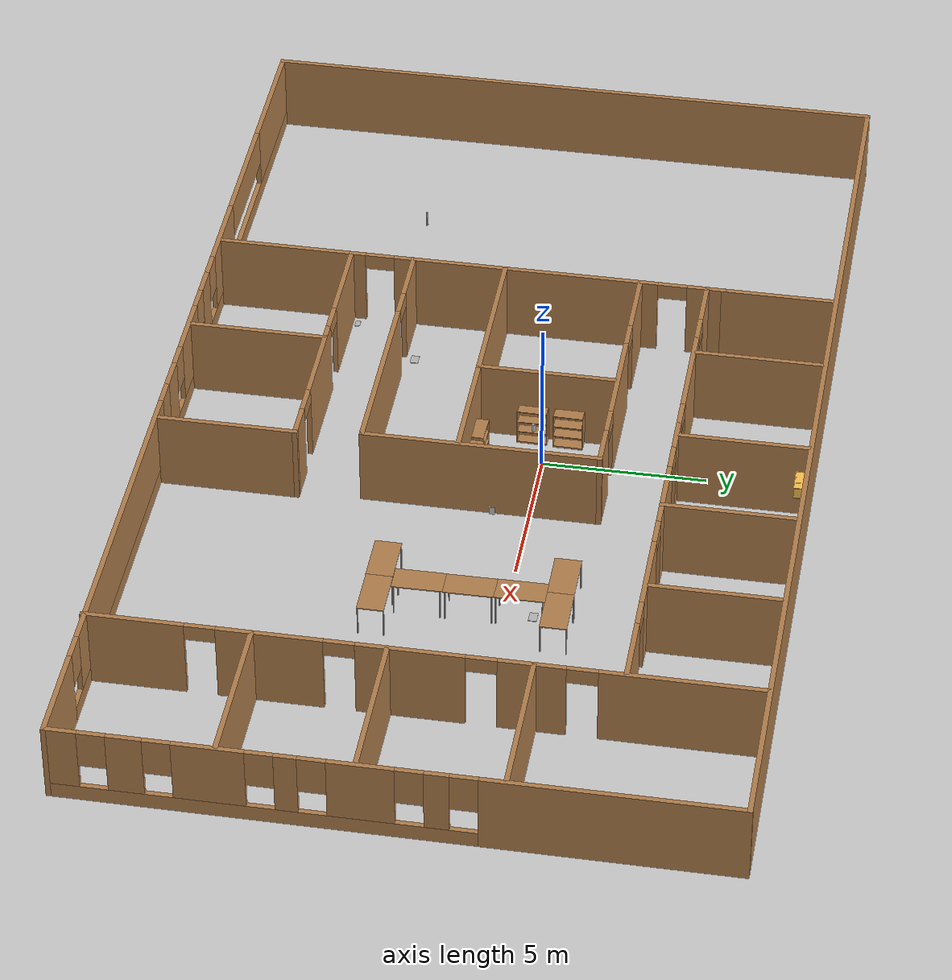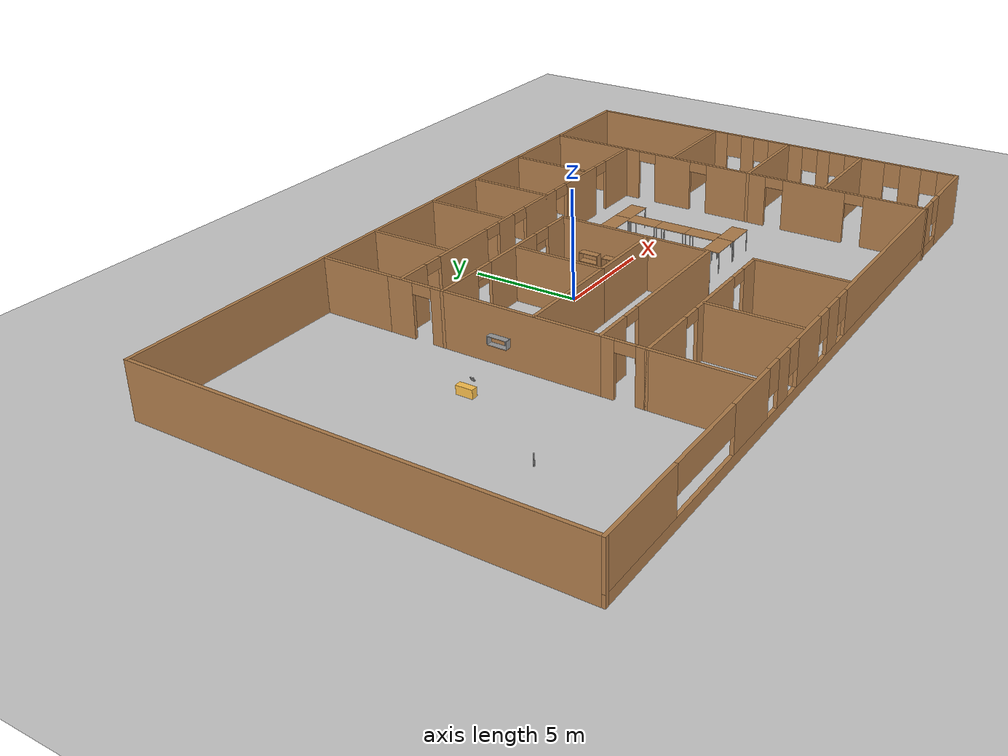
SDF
<sdf version="1.6">
 <world name="default">
  <light name="sun" type="directional">
   <pose>0 0 10 0 -0 0</pose>
   <diffuse>0.8 0.8 0.8 1</diffuse>
   <specular>0.2 0.2 0.2 1</specular>
   <attenuation>
    <range>1000</range>
    <constant>0.9</constant>
    <linear>0.01</linear>
    <quadratic>0.001</quadratic>
   </attenuation>
   <direction>-0.5 0.1 -0.9</direction>
  </light>
  <model name="ground_plane">
   <static>1</static>
   <link name="link">
    <collision name="collision">
     <geometry><plane><normal>0 0 1</normal><size>100 100</size></plane></geometry>
     <surface><friction><ode><mu>100</mu><mu2>50</mu2></ode></friction></surface>
    </collision>
    <visual name="visual">
     <cast_shadows>0</cast_shadows>
     <geometry><plane><normal>0 0 1</normal><size>100 100</size></plane></geometry>
     <material>
      <script><uri>file://media/materials/scripts/gazebo.material</uri><name>Gazebo/Grey</name></script>
     </material>
    </visual>
   </link>
  </model>
  <gravity>0 0 -9.8</gravity>
  <magnetic_field>6e-06 2.3e-05 -4.2e-05</magnetic_field>
  <atmosphere type="adiabatic"/>
  <physics name="default_physics" default="0" type="ode">
   <max_step_size>0.001</max_step_size>
   <real_time_factor>1</real_time_factor>
   <real_time_update_rate>1000</real_time_update_rate>
  </physics>
  <scene><ambient>0.4 0.4 0.4 1</ambient><background>0.7 0.7 0.7 1</background><shadows>1</shadows></scene>
  <spherical_coordinates>
   <surface_model>EARTH_WGS84</surface_model>
   <latitude_deg>0</latitude_deg>
   <longitude_deg>0</longitude_deg>
   <elevation>0</elevation>
   <heading_deg>0</heading_deg>
  </spherical_coordinates>
  <model name="Offices">
   <pose>0.0747 -1.55761 0 0 -0 0</pose>
   <link name="Wall_18">
    <collision name="Wall_18_Collision">
     <geometry><box><size>19.5 0.15 2.5</size></box></geometry>
     <pose>0 0 1.25 0 -0 0</pose>
    </collision>
    <visual name="Wall_18_Visual">
     <pose>0 0 1.25 0 -0 0</pose>
     <geometry><box><size>19.5 0.15 2.5</size></box></geometry>
     <material>
      <script><uri>file://media/materials/scripts/gazebo.material</uri><name>Gazebo/Wood</name></script>
      <ambient>1 1 1 1</ambient>
     </material>
     <meta><layer>0</layer></meta>
    </visual>
    <pose>-16.175 0.026818 0 0 -0 1.5708</pose>
   </link>
   <link name="Wall_19">
    <collision name="Wall_19_Collision">
     <geometry><box><size>32.5 0.15 2.5</size></box></geometry>
     <pose>0 0 1.25 0 -0 0</pose>
    </collision>
    <visual name="Wall_19_Visual">
     <pose>0 0 1.25 0 -0 0</pose>
     <geometry><box><size>32.5 0.15 2.5</size></box></geometry>
     <material>
      <script><uri>file://media/materials/scripts/gazebo.material</uri><name>Gazebo/Wood</name></script>
      <ambient>1 1 1 1</ambient>
     </material>
     <meta><layer>0</layer></meta>
    </visual>
    <pose>0 9.70182 0 0 -0 0</pose>
   </link>
   <link name="Wall_20">
    <pose>16.175 0.026818 0 0 0 -1.5708</pose>
    <visual name="Wall_20_Visual_0">
     <pose>-6.04317 0 1.25 0 -0 0</pose>
     <geometry><box><size>7.41367 0.15 2.5</size></box></geometry>
     <material>
      <script><uri>file://media/materials/scripts/gazebo.material</uri><name>Gazebo/Wood</name></script>
      <ambient>1 1 1 1</ambient>
     </material>
     <meta><layer>0</layer></meta>
    </visual>
    <collision name="Wall_20_Collision_0">
     <geometry><box><size>7.41367 0.15 2.5</size></box></geometry>
     <pose>-6.04317 0 1.25 0 -0 0</pose>
    </collision>
    <visual name="Wall_20_Visual_1">
     <pose>3.70683 0 0.25 0 -0 0</pose>
     <geometry><box><size>12.0863 0.15 0.5</size></box></geometry>
     <material>
      <script><uri>file://media/materials/scripts/gazebo.material</uri><name>Gazebo/Wood</name></script>
      <ambient>1 1 1 1</ambient>
     </material>
     <meta><layer>0</layer></meta>
    </visual>
    <collision name="Wall_20_Collision_1">
     <geometry><box><size>12.0863 0.15 0.5</size></box></geometry>
     <pose>3.70683 0 0.25 0 -0 0</pose>
    </collision>
    <visual name="Wall_20_Visual_2">
     <pose>-1.18542 0 1.5 0 -0 0</pose>
     <geometry><box><size>0.701813 0.15 2</size></box></geometry>
     <material>
      <script><uri>file://media/materials/scripts/gazebo.material</uri><name>Gazebo/Wood</name></script>
      <ambient>1 1 1 1</ambient>
     </material>
     <meta><layer>0</layer></meta>
    </visual>
    <collision name="Wall_20_Collision_2">
     <geometry><box><size>0.701813 0.15 2</size></box></geometry>
     <pose>-1.18542 0 1.5 0 -0 0</pose>
    </collision>
    <visual name="Wall_20_Visual_3">
     <pose>0.906388 0 1.5 0 -0 0</pose>
     <geometry><box><size>1.88181 0.15 2</size></box></geometry>
     <material>
      <script><uri>file://media/materials/scripts/gazebo.material</uri><name>Gazebo/Wood</name></script>
      <ambient>1 1 1 1</ambient>
     </material>
     <meta><layer>0</layer></meta>
    </visual>
    <collision name="Wall_20_Collision_3">
     <geometry><box><size>1.88181 0.15 2</size></box></geometry>
     <pose>0.906388 0 1.5 0 -0 0</pose>
    </collision>
    <visual name="Wall_20_Visual_4">
     <pose>2.97138 0 1.5 0 -0 0</pose>
     <geometry><box><size>0.648177 0.15 2</size></box></geometry>
     <material>
      <script><uri>file://media/materials/scripts/gazebo.material</uri><name>Gazebo/Wood</name></script>
      <ambient>1 1 1 1</ambient>
     </material>
     <meta><layer>0</layer></meta>
    </visual>
    <collision name="Wall_20_Collision_4">
     <geometry><box><size>0.648177 0.15 2</size></box></geometry>
     <pose>2.97138 0 1.5 0 -0 0</pose>
    </collision>
    <visual name="Wall_20_Visual_5">
     <pose>5.11683 0 1.5 0 -0 0</pose>
     <geometry><box><size>2.04272 0.15 2</size></box></geometry>
     <material>
      <script><uri>file://media/materials/scripts/gazebo.material</uri><name>Gazebo/Wood</name></script>
      <ambient>1 1 1 1</ambient>
     </material>
     <meta><layer>0</layer></meta>
    </visual>
    <collision name="Wall_20_Collision_5">
     <geometry><box><size>2.04272 0.15 2</size></box></geometry>
     <pose>5.11683 0 1.5 0 -0 0</pose>
    </collision>
    <visual name="Wall_20_Visual_6">
     <pose>7.45 0 1.5 0 -0 0</pose>
     <geometry><box><size>1.02363 0.15 2</size></box></geometry>
     <material>
      <script><uri>file://media/materials/scripts/gazebo.material</uri><name>Gazebo/Wood</name></script>
      <ambient>1 1 1 1</ambient>
     </material>
     <meta><layer>0</layer></meta>
    </visual>
    <collision name="Wall_20_Collision_6">
     <geometry><box><size>1.02363 0.15 2</size></box></geometry>
     <pose>7.45 0 1.5 0 -0 0</pose>
    </collision>
    <visual name="Wall_20_Visual_7">
     <pose>9.25591 0 1.5 0 -0 0</pose>
     <geometry><box><size>0.988181 0.15 2</size></box></geometry>
     <material>
      <script><uri>file://media/materials/scripts/gazebo.material</uri><name>Gazebo/Wood</name></script>
      <ambient>1 1 1 1</ambient>
     </material>
     <meta><layer>0</layer></meta>
    </visual>
    <collision name="Wall_20_Collision_7">
     <geometry><box><size>0.988181 0.15 2</size></box></geometry>
     <pose>9.25591 0 1.5 0 -0 0</pose>
    </collision>
    <visual name="Wall_20_Visual_8">
     <pose>-1.93633 0 1.9 0 -0 0</pose>
     <geometry><box><size>0.8 0.15 1.2</size></box></geometry>
     <material>
      <script><uri>file://media/materials/scripts/gazebo.material</uri><name>Gazebo/Wood</name></script>
      <ambient>1 1 1 1</ambient>
     </material>
     <meta><layer>0</layer></meta>
    </visual>
    <collision name="Wall_20_Collision_8">
     <geometry><box><size>0.8 0.15 1.2</size></box></geometry>
     <pose>-1.93633 0 1.9 0 -0 0</pose>
    </collision>
    <visual name="Wall_20_Visual_9">
     <pose>-0.434516 0 1.9 0 -0 0</pose>
     <geometry><box><size>0.8 0.15 1.2</size></box></geometry>
     <material>
      <script><uri>file://media/materials/scripts/gazebo.material</uri><name>Gazebo/Wood</name></script>
      <ambient>1 1 1 1</ambient>
     </material>
     <meta><layer>0</layer></meta>
    </visual>
    <collision name="Wall_20_Collision_9">
     <geometry><box><size>0.8 0.15 1.2</size></box></geometry>
     <pose>-0.434516 0 1.9 0 -0 0</pose>
    </collision>
    <visual name="Wall_20_Visual_10">
     <pose>2.24729 0 1.9 0 -0 0</pose>
     <geometry><box><size>0.8 0.15 1.2</size></box></geometry>
     <material>
      <script><uri>file://media/materials/scripts/gazebo.material</uri><name>Gazebo/Wood</name></script>
      <ambient>1 1 1 1</ambient>
     </material>
     <meta><layer>0</layer></meta>
    </visual>
    <collision name="Wall_20_Collision_10">
     <geometry><box><size>0.8 0.15 1.2</size></box></geometry>
     <pose>2.24729 0 1.9 0 -0 0</pose>
    </collision>
    <visual name="Wall_20_Visual_11">
     <pose>3.69547 0 1.9 0 -0 0</pose>
     <geometry><box><size>0.8 0.15 1.2</size></box></geometry>
     <material>
      <script><uri>file://media/materials/scripts/gazebo.material</uri><name>Gazebo/Wood</name></script>
      <ambient>1 1 1 1</ambient>
     </material>
     <meta><layer>0</layer></meta>
    </visual>
    <collision name="Wall_20_Collision_11">
     <geometry><box><size>0.8 0.15 1.2</size></box></geometry>
     <pose>3.69547 0 1.9 0 -0 0</pose>
    </collision>
    <visual name="Wall_20_Visual_12">
     <pose>6.53819 0 1.9 0 -0 0</pose>
     <geometry><box><size>0.8 0.15 1.2</size></box></geometry>
     <material>
      <script><uri>file://media/materials/scripts/gazebo.material</uri><name>Gazebo/Wood</name></script>
      <ambient>1 1 1 1</ambient>
     </material>
     <meta><layer>0</layer></meta>
    </visual>
    <collision name="Wall_20_Collision_12">
     <geometry><box><size>0.8 0.15 1.2</size></box></geometry>
     <pose>6.53819 0 1.9 0 -0 0</pose>
    </collision>
    <visual name="Wall_20_Visual_13">
     <pose>8.36182 0 1.9 0 -0 0</pose>
     <geometry><box><size>0.8 0.15 1.2</size></box></geometry>
     <material>
      <script><uri>file://media/materials/scripts/gazebo.material</uri><name>Gazebo/Wood</name></script>
      <ambient>1 1 1 1</ambient>
     </material>
     <meta><layer>0</layer></meta>
    </visual>
    <collision name="Wall_20_Collision_13">
     <geometry><box><size>0.8 0.15 1.2</size></box></geometry>
     <pose>8.36182 0 1.9 0 -0 0</pose>
    </collision>
   </link>
   <link name="Wall_21">
    <pose>0 -9.64818 0 0 -0 3.14159</pose>
    <visual name="Wall_21_Visual_0">
     <pose>-14.7397 0 1.25 0 -0 0</pose>
     <geometry><box><size>3.02057 0.15 2.5</size></box></geometry>
     <material>
      <script><uri>file://media/materials/scripts/gazebo.material</uri><name>Gazebo/Wood</name></script>
      <ambient>1 1 1 1</ambient>
     </material>
     <meta><layer>0</layer></meta>
    </visual>
    <collision name="Wall_21_Collision_0">
     <geometry><box><size>3.02057 0.15 2.5</size></box></geometry>
     <pose>-14.7397 0 1.25 0 -0 0</pose>
    </collision>
    <visual name="Wall_21_Visual_1">
     <pose>1.51029 0 0.25 0 -0 0</pose>
     <geometry><box><size>29.4794 0.15 0.5</size></box></geometry>
     <material>
      <script><uri>file://media/materials/scripts/gazebo.material</uri><name>Gazebo/Wood</name></script>
      <ambient>1 1 1 1</ambient>
     </material>
     <meta><layer>0</layer></meta>
    </visual>
    <collision name="Wall_21_Collision_1">
     <geometry><box><size>29.4794 0.15 0.5</size></box></geometry>
     <pose>1.51029 0 0.25 0 -0 0</pose>
    </collision>
    <visual name="Wall_21_Visual_2">
     <pose>-7.14399 0 1.5 0 -0 0</pose>
     <geometry><box><size>10.5709 0.15 2</size></box></geometry>
     <material>
      <script><uri>file://media/materials/scripts/gazebo.material</uri><name>Gazebo/Wood</name></script>
      <ambient>1 1 1 1</ambient>
     </material>
     <meta><layer>0</layer></meta>
    </visual>
    <collision name="Wall_21_Collision_2">
     <geometry><box><size>10.5709 0.15 2</size></box></geometry>
     <pose>-7.14399 0 1.5 0 -0 0</pose>
    </collision>
    <visual name="Wall_21_Visual_3">
     <pose>-0.546741 0 1.5 0 -0 0</pose>
     <geometry><box><size>1.02363 0.15 2</size></box></geometry>
     <material>
      <script><uri>file://media/materials/scripts/gazebo.material</uri><name>Gazebo/Wood</name></script>
      <ambient>1 1 1 1</ambient>
     </material>
     <meta><layer>0</layer></meta>
    </visual>
    <collision name="Wall_21_Collision_3">
     <geometry><box><size>1.02363 0.15 2</size></box></geometry>
     <pose>-0.546741 0 1.5 0 -0 0</pose>
    </collision>
    <visual name="Wall_21_Visual_4">
     <pose>1.78643 0 1.5 0 -0 0</pose>
     <geometry><box><size>2.04272 0.15 2</size></box></geometry>
     <material>
      <script><uri>file://media/materials/scripts/gazebo.material</uri><name>Gazebo/Wood</name></script>
      <ambient>1 1 1 1</ambient>
     </material>
     <meta><layer>0</layer></meta>
    </visual>
    <collision name="Wall_21_Collision_4">
     <geometry><box><size>2.04272 0.15 2</size></box></geometry>
     <pose>1.78643 0 1.5 0 -0 0</pose>
    </collision>
    <visual name="Wall_21_Visual_5">
     <pose>4.06597 0 1.5 0 -0 0</pose>
     <geometry><box><size>0.916358 0.15 2</size></box></geometry>
     <material>
      <script><uri>file://media/materials/scripts/gazebo.material</uri><name>Gazebo/Wood</name></script>
      <ambient>1 1 1 1</ambient>
     </material>
     <meta><layer>0</layer></meta>
    </visual>
    <collision name="Wall_21_Collision_5">
     <geometry><box><size>0.916358 0.15 2</size></box></geometry>
     <pose>4.06597 0 1.5 0 -0 0</pose>
    </collision>
    <visual name="Wall_21_Visual_6">
     <pose>6.67187 0 1.5 0 -0 0</pose>
     <geometry><box><size>2.69544 0.15 2</size></box></geometry>
     <material>
      <script><uri>file://media/materials/scripts/gazebo.material</uri><name>Gazebo/Wood</name></script>
      <ambient>1 1 1 1</ambient>
     </material>
     <meta><layer>0</layer></meta>
    </visual>
    <collision name="Wall_21_Collision_6">
     <geometry><box><size>2.69544 0.15 2</size></box></geometry>
     <pose>6.67187 0 1.5 0 -0 0</pose>
    </collision>
    <visual name="Wall_21_Visual_7">
     <pose>14.1348 0 1.5 0 -0 0</pose>
     <geometry><box><size>4.23041 0.15 2</size></box></geometry>
     <material>
      <script><uri>file://media/materials/scripts/gazebo.material</uri><name>Gazebo/Wood</name></script>
      <ambient>1 1 1 1</ambient>
     </material>
     <meta><layer>0</layer></meta>
    </visual>
    <collision name="Wall_21_Collision_7">
     <geometry><box><size>4.23041 0.15 2</size></box></geometry>
     <pose>14.1348 0 1.5 0 -0 0</pose>
    </collision>
    <visual name="Wall_21_Visual_8">
     <pose>-12.8294 0 1.9 0 -0 0</pose>
     <geometry><box><size>0.8 0.15 1.2</size></box></geometry>
     <material>
      <script><uri>file://media/materials/scripts/gazebo.material</uri><name>Gazebo/Wood</name></script>
      <ambient>1 1 1 1</ambient>
     </material>
     <meta><layer>0</layer></meta>
    </visual>
    <collision name="Wall_21_Collision_8">
     <geometry><box><size>0.8 0.15 1.2</size></box></geometry>
     <pose>-12.8294 0 1.9 0 -0 0</pose>
    </collision>
    <visual name="Wall_21_Visual_9">
     <pose>-1.45856 0 1.9 0 -0 0</pose>
     <geometry><box><size>0.8 0.15 1.2</size></box></geometry>
     <material>
      <script><uri>file://media/materials/scripts/gazebo.material</uri><name>Gazebo/Wood</name></script>
      <ambient>1 1 1 1</ambient>
     </material>
     <meta><layer>0</layer></meta>
    </visual>
    <collision name="Wall_21_Collision_9">
     <geometry><box><size>0.8 0.15 1.2</size></box></geometry>
     <pose>-1.45856 0 1.9 0 -0 0</pose>
    </collision>
    <visual name="Wall_21_Visual_10">
     <pose>0.365075 0 1.9 0 -0 0</pose>
     <geometry><box><size>0.8 0.15 1.2</size></box></geometry>
     <material>
      <script><uri>file://media/materials/scripts/gazebo.material</uri><name>Gazebo/Wood</name></script>
      <ambient>1 1 1 1</ambient>
     </material>
     <meta><layer>0</layer></meta>
    </visual>
    <collision name="Wall_21_Collision_10">
     <geometry><box><size>0.8 0.15 1.2</size></box></geometry>
     <pose>0.365075 0 1.9 0 -0 0</pose>
    </collision>
    <visual name="Wall_21_Visual_11">
     <pose>3.20779 0 1.9 0 -0 0</pose>
     <geometry><box><size>0.8 0.15 1.2</size></box></geometry>
     <material>
      <script><uri>file://media/materials/scripts/gazebo.material</uri><name>Gazebo/Wood</name></script>
      <ambient>1 1 1 1</ambient>
     </material>
     <meta><layer>0</layer></meta>
    </visual>
    <collision name="Wall_21_Collision_11">
     <geometry><box><size>0.8 0.15 1.2</size></box></geometry>
     <pose>3.20779 0 1.9 0 -0 0</pose>
    </collision>
    <visual name="Wall_21_Visual_12">
     <pose>4.92415 0 1.9 0 -0 0</pose>
     <geometry><box><size>0.8 0.15 1.2</size></box></geometry>
     <material>
      <script><uri>file://media/materials/scripts/gazebo.material</uri><name>Gazebo/Wood</name></script>
      <ambient>1 1 1 1</ambient>
     </material>
     <meta><layer>0</layer></meta>
    </visual>
    <collision name="Wall_21_Collision_12">
     <geometry><box><size>0.8 0.15 1.2</size></box></geometry>
     <pose>4.92415 0 1.9 0 -0 0</pose>
    </collision>
    <visual name="Wall_21_Visual_13">
     <pose>10.0196 0 1.9 0 -0 0</pose>
     <geometry><box><size>4 0.15 1.2</size></box></geometry>
     <material>
      <script><uri>file://media/materials/scripts/gazebo.material</uri><name>Gazebo/Wood</name></script>
      <ambient>1 1 1 1</ambient>
     </material>
     <meta><layer>0</layer></meta>
    </visual>
    <collision name="Wall_21_Collision_13">
     <geometry><box><size>4 0.15 1.2</size></box></geometry>
     <pose>10.0196 0 1.9 0 -0 0</pose>
    </collision>
   </link>
   <link name="Wall_24">
    <pose>11.4476 -0.026818 0 0 -0 1.5708</pose>
    <visual name="Wall_24_Visual_0">
     <pose>-8.26182 0 1.25 0 -0 0</pose>
     <geometry><box><size>2.97636 0.15 2.5</size></box></geometry>
     <material>
      <script><uri>file://media/materials/scripts/gazebo.material</uri><name>Gazebo/Wood</name></script>
      <ambient>1 1 1 1</ambient>
     </material>
     <meta><layer>0</layer></meta>
    </visual>
    <collision name="Wall_24_Collision_0">
     <geometry><box><size>2.97636 0.15 2.5</size></box></geometry>
     <pose>-8.26182 0 1.25 0 -0 0</pose>
    </collision>
    <visual name="Wall_24_Visual_1">
     <pose>-4.3391 0 1.25 0 -0 0</pose>
     <geometry><box><size>3.06908 0.15 2.5</size></box></geometry>
     <material>
      <script><uri>file://media/materials/scripts/gazebo.material</uri><name>Gazebo/Wood</name></script>
      <ambient>1 1 1 1</ambient>
     </material>
     <meta><layer>0</layer></meta>
    </visual>
    <collision name="Wall_24_Collision_1">
     <geometry><box><size>3.06908 0.15 2.5</size></box></geometry>
     <pose>-4.3391 0 1.25 0 -0 0</pose>
    </collision>
    <visual name="Wall_24_Visual_2">
     <pose>-0.343209 0 1.25 0 -0 0</pose>
     <geometry><box><size>3.12271 0.15 2.5</size></box></geometry>
     <material>
      <script><uri>file://media/materials/scripts/gazebo.material</uri><name>Gazebo/Wood</name></script>
      <ambient>1 1 1 1</ambient>
     </material>
     <meta><layer>0</layer></meta>
    </visual>
    <collision name="Wall_24_Collision_2">
     <geometry><box><size>3.12271 0.15 2.5</size></box></geometry>
     <pose>-0.343209 0 1.25 0 -0 0</pose>
    </collision>
    <visual name="Wall_24_Visual_3">
     <pose>3.08951 0 1.25 0 -0 0</pose>
     <geometry><box><size>1.94272 0.15 2.5</size></box></geometry>
     <material>
      <script><uri>file://media/materials/scripts/gazebo.material</uri><name>Gazebo/Wood</name></script>
      <ambient>1 1 1 1</ambient>
     </material>
     <meta><layer>0</layer></meta>
    </visual>
    <collision name="Wall_24_Collision_3">
     <geometry><box><size>1.94272 0.15 2.5</size></box></geometry>
     <pose>3.08951 0 1.25 0 -0 0</pose>
    </collision>
    <visual name="Wall_24_Visual_4">
     <pose>7.35543 0 1.25 0 -0 0</pose>
     <geometry><box><size>4.78913 0.15 2.5</size></box></geometry>
     <material>
      <script><uri>file://media/materials/scripts/gazebo.material</uri><name>Gazebo/Wood</name></script>
      <ambient>1 1 1 1</ambient>
     </material>
     <meta><layer>0</layer></meta>
    </visual>
    <collision name="Wall_24_Collision_4">
     <geometry><box><size>4.78913 0.15 2.5</size></box></geometry>
     <pose>7.35543 0 1.25 0 -0 0</pose>
    </collision>
    <visual name="Wall_24_Visual_5">
     <pose>-6.32364 0 2.25 0 -0 0</pose>
     <geometry><box><size>0.9 0.15 0.5</size></box></geometry>
     <material>
      <script><uri>file://media/materials/scripts/gazebo.material</uri><name>Gazebo/Wood</name></script>
      <ambient>1 1 1 1</ambient>
     </material>
     <meta><layer>0</layer></meta>
    </visual>
    <collision name="Wall_24_Collision_5">
     <geometry><box><size>0.9 0.15 0.5</size></box></geometry>
     <pose>-6.32364 0 2.25 0 -0 0</pose>
    </collision>
    <visual name="Wall_24_Visual_6">
     <pose>-2.35457 0 2.25 0 -0 0</pose>
     <geometry><box><size>0.9 0.15 0.5</size></box></geometry>
     <material>
      <script><uri>file://media/materials/scripts/gazebo.material</uri><name>Gazebo/Wood</name></script>
      <ambient>1 1 1 1</ambient>
     </material>
     <meta><layer>0</layer></meta>
    </visual>
    <collision name="Wall_24_Collision_6">
     <geometry><box><size>0.9 0.15 0.5</size></box></geometry>
     <pose>-2.35457 0 2.25 0 -0 0</pose>
    </collision>
    <visual name="Wall_24_Visual_7">
     <pose>1.66815 0 2.25 0 -0 0</pose>
     <geometry><box><size>0.9 0.15 0.5</size></box></geometry>
     <material>
      <script><uri>file://media/materials/scripts/gazebo.material</uri><name>Gazebo/Wood</name></script>
      <ambient>1 1 1 1</ambient>
     </material>
     <meta><layer>0</layer></meta>
    </visual>
    <collision name="Wall_24_Collision_7">
     <geometry><box><size>0.9 0.15 0.5</size></box></geometry>
     <pose>1.66815 0 2.25 0 -0 0</pose>
    </collision>
    <visual name="Wall_24_Visual_8">
     <pose>4.51087 0 2.25 0 -0 0</pose>
     <geometry><box><size>0.9 0.15 0.5</size></box></geometry>
     <material>
      <script><uri>file://media/materials/scripts/gazebo.material</uri><name>Gazebo/Wood</name></script>
      <ambient>1 1 1 1</ambient>
     </material>
     <meta><layer>0</layer></meta>
    </visual>
    <collision name="Wall_24_Collision_8">
     <geometry><box><size>0.9 0.15 0.5</size></box></geometry>
     <pose>4.51087 0 2.25 0 -0 0</pose>
    </collision>
   </link>
   <link name="Wall_26">
    <collision name="Wall_26_Collision">
     <geometry><box><size>4.75 0.15 2.5</size></box></geometry>
     <pose>0 0 1.25 0 -0 0</pose>
    </collision>
    <visual name="Wall_26_Visual">
     <pose>0 0 1.25 0 -0 0</pose>
     <geometry><box><size>4.75 0.15 2.5</size></box></geometry>
     <material>
      <script><uri>file://media/materials/scripts/gazebo.material</uri><name>Gazebo/Wood</name></script>
      <ambient>1 1 1 1</ambient>
     </material>
     <meta><layer>0</layer></meta>
    </visual>
    <pose>13.8013 -4.87456 0 0 -0 0</pose>
   </link>
   <link name="Wall_28">
    <collision name="Wall_28_Collision">
     <geometry><box><size>4.75 0.15 2.5</size></box></geometry>
     <pose>0 0 1.25 0 -0 0</pose>
    </collision>
    <visual name="Wall_28_Visual">
     <pose>0 0 1.25 0 -0 0</pose>
     <geometry><box><size>4.75 0.15 2.5</size></box></geometry>
     <material>
      <script><uri>file://media/materials/scripts/gazebo.material</uri><name>Gazebo/Wood</name></script>
      <ambient>1 1 1 1</ambient>
     </material>
     <meta><layer>0</layer></meta>
    </visual>
    <pose>13.7476 -1.01276 0 0 -0 0</pose>
   </link>
   <link name="Wall_30">
    <collision name="Wall_30_Collision">
     <geometry><box><size>4.75 0.15 2.5</size></box></geometry>
     <pose>0 0 1.25 0 -0 0</pose>
    </collision>
    <visual name="Wall_30_Visual">
     <pose>0 0 1.25 0 -0 0</pose>
     <geometry><box><size>4.75 0.15 2.5</size></box></geometry>
     <material>
      <script><uri>file://media/materials/scripts/gazebo.material</uri><name>Gazebo/Wood</name></script>
      <ambient>1 1 1 1</ambient>
     </material>
     <meta><layer>0</layer></meta>
    </visual>
    <pose>13.8013 3.11723 0 0 -0 0</pose>
   </link>
   <link name="Wall_32">
    <collision name="Wall_32_Collision">
     <geometry><box><size>4.25 0.15 2.5</size></box></geometry>
     <pose>0 0 1.25 0 -0 0</pose>
    </collision>
    <visual name="Wall_32_Visual">
     <pose>0 0 1.25 0 -0 0</pose>
     <geometry><box><size>4.25 0.15 2.5</size></box></geometry>
     <material>
      <script><uri>file://media/materials/scripts/gazebo.material</uri><name>Gazebo/Wood</name></script>
      <ambient>1 1 1 1</ambient>
     </material>
     <meta><layer>0</layer></meta>
    </visual>
    <pose>2.61644 -7.47291 0 0 -0 1.5708</pose>
   </link>
   <link name="Wall_33">
    <pose>-1.80856 -5.42291 0 0 -0 3.14159</pose>
    <visual name="Wall_33_Visual_0">
     <pose>-3.92083 0 1.25 0 -0 0</pose>
     <geometry><box><size>1.15834 0.15 2.5</size></box></geometry>
     <material>
      <script><uri>file://media/materials/scripts/gazebo.material</uri><name>Gazebo/Wood</name></script>
      <ambient>1 1 1 1</ambient>
     </material>
     <meta><layer>0</layer></meta>
    </visual>
    <collision name="Wall_33_Collision_0">
     <geometry><box><size>1.15834 0.15 2.5</size></box></geometry>
     <pose>-3.92083 0 1.25 0 -0 0</pose>
    </collision>
    <visual name="Wall_33_Visual_1">
     <pose>-0.880306 0 1.25 0 -0 0</pose>
     <geometry><box><size>3.12271 0.15 2.5</size></box></geometry>
     <material>
      <script><uri>file://media/materials/scripts/gazebo.material</uri><name>Gazebo/Wood</name></script>
      <ambient>1 1 1 1</ambient>
     </material>
     <meta><layer>0</layer></meta>
    </visual>
    <collision name="Wall_33_Collision_1">
     <geometry><box><size>3.12271 0.15 2.5</size></box></geometry>
     <pose>-0.880306 0 1.25 0 -0 0</pose>
    </collision>
    <visual name="Wall_33_Visual_2">
     <pose>3.04053 0 1.25 0 -0 0</pose>
     <geometry><box><size>2.91895 0.15 2.5</size></box></geometry>
     <material>
      <script><uri>file://media/materials/scripts/gazebo.material</uri><name>Gazebo/Wood</name></script>
      <ambient>1 1 1 1</ambient>
     </material>
     <meta><layer>0</layer></meta>
    </visual>
    <collision name="Wall_33_Collision_2">
     <geometry><box><size>2.91895 0.15 2.5</size></box></geometry>
     <pose>3.04053 0 1.25 0 -0 0</pose>
    </collision>
    <visual name="Wall_33_Visual_3">
     <pose>-2.89166 0 2.25 0 -0 0</pose>
     <geometry><box><size>0.9 0.15 0.5</size></box></geometry>
     <material>
      <script><uri>file://media/materials/scripts/gazebo.material</uri><name>Gazebo/Wood</name></script>
      <ambient>1 1 1 1</ambient>
     </material>
     <meta><layer>0</layer></meta>
    </visual>
    <collision name="Wall_33_Collision_3">
     <geometry><box><size>0.9 0.15 0.5</size></box></geometry>
     <pose>-2.89166 0 2.25 0 -0 0</pose>
    </collision>
    <visual name="Wall_33_Visual_4">
     <pose>1.13105 0 2.25 0 -0 0</pose>
     <geometry><box><size>0.9 0.15 0.5</size></box></geometry>
     <material>
      <script><uri>file://media/materials/scripts/gazebo.material</uri><name>Gazebo/Wood</name></script>
      <ambient>1 1 1 1</ambient>
     </material>
     <meta><layer>0</layer></meta>
    </visual>
    <collision name="Wall_33_Collision_4">
     <geometry><box><size>0.9 0.15 0.5</size></box></geometry>
     <pose>1.13105 0 2.25 0 -0 0</pose>
    </collision>
   </link>
   <link name="Wall_34">
    <collision name="Wall_34_Collision">
     <geometry><box><size>4.25 0.15 2.5</size></box></geometry>
     <pose>0 0 1.25 0 -0 0</pose>
    </collision>
    <visual name="Wall_34_Visual">
     <pose>0 0 1.25 0 -0 0</pose>
     <geometry><box><size>4.25 0.15 2.5</size></box></geometry>
     <material>
      <script><uri>file://media/materials/scripts/gazebo.material</uri><name>Gazebo/Wood</name></script>
      <ambient>1 1 1 1</ambient>
     </material>
     <meta><layer>0</layer></meta>
    </visual>
    <pose>-6.23356 -7.47291 0 0 0 -1.5708</pose>
   </link>
   <link name="Wall_38">
    <collision name="Wall_38_Collision">
     <geometry><box><size>4.25 0.15 2.5</size></box></geometry>
     <pose>0 0 1.25 0 -0 0</pose>
    </collision>
    <visual name="Wall_38_Visual">
     <pose>0 0 1.25 0 -0 0</pose>
     <geometry><box><size>4.25 0.15 2.5</size></box></geometry>
     <material>
      <script><uri>file://media/materials/scripts/gazebo.material</uri><name>Gazebo/Wood</name></script>
      <ambient>1 1 1 1</ambient>
     </material>
     <meta><layer>0</layer></meta>
    </visual>
    <pose>-1.94264 -7.49656 0 0 0 -1.5708</pose>
   </link>
   <link name="Wall_40">
    <pose>-1.93353 -3.46202 0 0 -0 0</pose>
    <visual name="Wall_40_Visual_0">
     <pose>-3.4519 0 1.25 0 -0 0</pose>
     <geometry><box><size>1.8462 0.15 2.5</size></box></geometry>
     <material>
      <script><uri>file://media/materials/scripts/gazebo.material</uri><name>Gazebo/Wood</name></script>
      <ambient>1 1 1 1</ambient>
     </material>
     <meta><layer>0</layer></meta>
    </visual>
    <collision name="Wall_40_Collision_0">
     <geometry><box><size>1.8462 0.15 2.5</size></box></geometry>
     <pose>-3.4519 0 1.25 0 -0 0</pose>
    </collision>
    <visual name="Wall_40_Visual_1">
     <pose>1.3731 0 1.25 0 -0 0</pose>
     <geometry><box><size>6.0038 0.15 2.5</size></box></geometry>
     <material>
      <script><uri>file://media/materials/scripts/gazebo.material</uri><name>Gazebo/Wood</name></script>
      <ambient>1 1 1 1</ambient>
     </material>
     <meta><layer>0</layer></meta>
    </visual>
    <collision name="Wall_40_Collision_1">
     <geometry><box><size>6.0038 0.15 2.5</size></box></geometry>
     <pose>1.3731 0 1.25 0 -0 0</pose>
    </collision>
    <visual name="Wall_40_Visual_2">
     <pose>-2.0788 0 2.25 0 -0 0</pose>
     <geometry><box><size>0.9 0.15 0.5</size></box></geometry>
     <material>
      <script><uri>file://media/materials/scripts/gazebo.material</uri><name>Gazebo/Wood</name></script>
      <ambient>1 1 1 1</ambient>
     </material>
     <meta><layer>0</layer></meta>
    </visual>
    <collision name="Wall_40_Collision_2">
     <geometry><box><size>0.9 0.15 0.5</size></box></geometry>
     <pose>-2.0788 0 2.25 0 -0 0</pose>
    </collision>
   </link>
   <link name="Wall_49">
    <collision name="Wall_49_Collision">
     <geometry><box><size>7.25 0.15 2.5</size></box></geometry>
     <pose>0 0 1.25 0 -0 0</pose>
    </collision>
    <visual name="Wall_49_Visual">
     <pose>0 0 1.25 0 -0 0</pose>
     <geometry><box><size>7.25 0.15 2.5</size></box></geometry>
     <material>
      <script><uri>file://media/materials/scripts/gazebo.material</uri><name>Gazebo/Wood</name></script>
      <ambient>1 1 1 1</ambient>
     </material>
     <meta><layer>0</layer></meta>
    </visual>
    <pose>2.36647 0.08798 0 0 -0 1.5708</pose>
   </link>
   <link name="Wall_50">
    <pose>-1.93353 3.63798 0 0 -0 3.14159</pose>
    <visual name="Wall_50_Visual_0">
     <pose>-3.67945 0 1.25 0 -0 0</pose>
     <geometry><box><size>1.39109 0.15 2.5</size></box></geometry>
     <material>
      <script><uri>file://media/materials/scripts/gazebo.material</uri><name>Gazebo/Wood</name></script>
      <ambient>1 1 1 1</ambient>
     </material>
     <meta><layer>0</layer></meta>
    </visual>
    <collision name="Wall_50_Collision_0">
     <geometry><box><size>1.39109 0.15 2.5</size></box></geometry>
     <pose>-3.67945 0 1.25 0 -0 0</pose>
    </collision>
    <visual name="Wall_50_Visual_1">
     <pose>-0.442097 0 1.25 0 -0 0</pose>
     <geometry><box><size>3.28362 0.15 2.5</size></box></geometry>
     <material>
      <script><uri>file://media/materials/scripts/gazebo.material</uri><name>Gazebo/Wood</name></script>
      <ambient>1 1 1 1</ambient>
     </material>
     <meta><layer>0</layer></meta>
    </visual>
    <collision name="Wall_50_Collision_1">
     <geometry><box><size>3.28362 0.15 2.5</size></box></geometry>
     <pose>-0.442097 0 1.25 0 -0 0</pose>
    </collision>
    <visual name="Wall_50_Visual_2">
     <pose>3.23736 0 1.25 0 -0 0</pose>
     <geometry><box><size>2.27529 0.15 2.5</size></box></geometry>
     <material>
      <script><uri>file://media/materials/scripts/gazebo.material</uri><name>Gazebo/Wood</name></script>
      <ambient>1 1 1 1</ambient>
     </material>
     <meta><layer>0</layer></meta>
    </visual>
    <collision name="Wall_50_Collision_2">
     <geometry><box><size>2.27529 0.15 2.5</size></box></geometry>
     <pose>3.23736 0 1.25 0 -0 0</pose>
    </collision>
    <visual name="Wall_50_Visual_3">
     <pose>-2.53391 0 2.25 0 -0 0</pose>
     <geometry><box><size>0.9 0.15 0.5</size></box></geometry>
     <material>
      <script><uri>file://media/materials/scripts/gazebo.material</uri><name>Gazebo/Wood</name></script>
      <ambient>1 1 1 1</ambient>
     </material>
     <meta><layer>0</layer></meta>
    </visual>
    <collision name="Wall_50_Collision_3">
     <geometry><box><size>0.9 0.15 0.5</size></box></geometry>
     <pose>-2.53391 0 2.25 0 -0 0</pose>
    </collision>
    <visual name="Wall_50_Visual_4">
     <pose>1.64971 0 2.25 0 -0 0</pose>
     <geometry><box><size>0.9 0.15 0.5</size></box></geometry>
     <material>
      <script><uri>file://media/materials/scripts/gazebo.material</uri><name>Gazebo/Wood</name></script>
      <ambient>1 1 1 1</ambient>
     </material>
     <meta><layer>0</layer></meta>
    </visual>
    <collision name="Wall_50_Collision_4">
     <geometry><box><size>0.9 0.15 0.5</size></box></geometry>
     <pose>1.64971 0 2.25 0 -0 0</pose>
    </collision>
   </link>
   <link name="Wall_53">
    <collision name="Wall_53_Collision">
     <geometry><box><size>7.25 0.15 2.5</size></box></geometry>
     <pose>0 0 1.25 0 -0 0</pose>
    </collision>
    <visual name="Wall_53_Visual">
     <pose>0 0 1.25 0 -0 0</pose>
     <geometry><box><size>7.25 0.15 2.5</size></box></geometry>
     <material>
      <script><uri>file://media/materials/scripts/gazebo.material</uri><name>Gazebo/Wood</name></script>
      <ambient>1 1 1 1</ambient>
     </material>
     <meta><layer>0</layer></meta>
    </visual>
    <pose>-6.23353 0.08798 0 0 0 -1.5708</pose>
   </link>
   <link name="Wall_56">
    <pose>-6.23355 -4.44247 0 0 -0 1.57078</pose>
    <visual name="Wall_56_Visual_0">
     <pose>-0.794908 0 1.25 0 -0 0</pose>
     <geometry><box><size>0.521074 0.15 2.5</size></box></geometry>
     <material>
      <script><uri>file://media/materials/scripts/gazebo.material</uri><name>Gazebo/Wood</name></script>
      <ambient>1 1 1 1</ambient>
     </material>
     <meta><layer>0</layer></meta>
    </visual>
    <collision name="Wall_56_Collision_0">
     <geometry><box><size>0.521074 0.15 2.5</size></box></geometry>
     <pose>-0.794908 0 1.25 0 -0 0</pose>
    </collision>
    <visual name="Wall_56_Visual_1">
     <pose>0.710537 0 1.25 0 -0 0</pose>
     <geometry><box><size>0.689816 0.15 2.5</size></box></geometry>
     <material>
      <script><uri>file://media/materials/scripts/gazebo.material</uri><name>Gazebo/Wood</name></script>
      <ambient>1 1 1 1</ambient>
     </material>
     <meta><layer>0</layer></meta>
    </visual>
    <collision name="Wall_56_Collision_1">
     <geometry><box><size>0.689816 0.15 2.5</size></box></geometry>
     <pose>0.710537 0 1.25 0 -0 0</pose>
    </collision>
    <visual name="Wall_56_Visual_2">
     <pose>-0.084371 0 2.25 0 -0 0</pose>
     <geometry><box><size>0.9 0.15 0.5</size></box></geometry>
     <material>
      <script><uri>file://media/materials/scripts/gazebo.material</uri><name>Gazebo/Wood</name></script>
      <ambient>1 1 1 1</ambient>
     </material>
     <meta><layer>0</layer></meta>
    </visual>
    <collision name="Wall_56_Collision_2">
     <geometry><box><size>0.9 0.15 0.5</size></box></geometry>
     <pose>-0.084371 0 2.25 0 -0 0</pose>
    </collision>
   </link>
   <link name="Wall_58">
    <pose>-6.23353 4.93798 0 0 -0 1.5708</pose>
    <visual name="Wall_58_Visual_0">
     <pose>-1.05901 0 1.25 0 -0 0</pose>
     <geometry><box><size>0.631977 0.15 2.5</size></box></geometry>
     <material>
      <script><uri>file://media/materials/scripts/gazebo.material</uri><name>Gazebo/Wood</name></script>
      <ambient>1 1 1 1</ambient>
     </material>
     <meta><layer>0</layer></meta>
    </visual>
    <collision name="Wall_58_Collision_0">
     <geometry><box><size>0.631977 0.15 2.5</size></box></geometry>
     <pose>-1.05901 0 1.25 0 -0 0</pose>
    </collision>
    <visual name="Wall_58_Visual_1">
     <pose>0.765989 0 1.25 0 -0 0</pose>
     <geometry><box><size>1.21802 0.15 2.5</size></box></geometry>
     <material>
      <script><uri>file://media/materials/scripts/gazebo.material</uri><name>Gazebo/Wood</name></script>
      <ambient>1 1 1 1</ambient>
     </material>
     <meta><layer>0</layer></meta>
    </visual>
    <collision name="Wall_58_Collision_1">
     <geometry><box><size>1.21802 0.15 2.5</size></box></geometry>
     <pose>0.765989 0 1.25 0 -0 0</pose>
    </collision>
    <visual name="Wall_58_Visual_2">
     <pose>-0.293023 0 2.25 0 -0 0</pose>
     <geometry><box><size>0.9 0.15 0.5</size></box></geometry>
     <material>
      <script><uri>file://media/materials/scripts/gazebo.material</uri><name>Gazebo/Wood</name></script>
      <ambient>1 1 1 1</ambient>
     </material>
     <meta><layer>0</layer></meta>
    </visual>
    <collision name="Wall_58_Collision_2">
     <geometry><box><size>0.9 0.15 0.5</size></box></geometry>
     <pose>-0.293023 0 2.25 0 -0 0</pose>
    </collision>
   </link>
   <link name="Wall_59">
    <collision name="Wall_59_Collision">
     <geometry><box><size>3.5 0.15 2.5</size></box></geometry>
     <pose>0 0 1.25 0 -0 0</pose>
    </collision>
    <visual name="Wall_59_Visual">
     <pose>0 0 1.25 0 -0 0</pose>
     <geometry><box><size>3.5 0.15 2.5</size></box></geometry>
     <material>
      <script><uri>file://media/materials/scripts/gazebo.material</uri><name>Gazebo/Wood</name></script>
      <ambient>1 1 1 1</ambient>
     </material>
     <meta><layer>0</layer></meta>
    </visual>
    <pose>-6.23353 7.91298 0 0 -0 1.5708</pose>
   </link>
   <link name="Wall_62">
    <pose>2.56647 5.70977 0 0 -0 0</pose>
    <visual name="Wall_62_Visual_0">
     <pose>-8.05917 0 1.25 0 -0 0</pose>
     <geometry><box><size>1.63165 0.15 2.5</size></box></geometry>
     <material>
      <script><uri>file://media/materials/scripts/gazebo.material</uri><name>Gazebo/Wood</name></script>
      <ambient>1 1 1 1</ambient>
     </material>
     <meta><layer>0</layer></meta>
    </visual>
    <collision name="Wall_62_Collision_0">
     <geometry><box><size>1.63165 0.15 2.5</size></box></geometry>
     <pose>-8.05917 0 1.25 0 -0 0</pose>
    </collision>
    <visual name="Wall_62_Visual_1">
     <pose>-4.72835 0 1.25 0 -0 0</pose>
     <geometry><box><size>3.22999 0.15 2.5</size></box></geometry>
     <material>
      <script><uri>file://media/materials/scripts/gazebo.material</uri><name>Gazebo/Wood</name></script>
      <ambient>1 1 1 1</ambient>
     </material>
     <meta><layer>0</layer></meta>
    </visual>
    <collision name="Wall_62_Collision_1">
     <geometry><box><size>3.22999 0.15 2.5</size></box></geometry>
     <pose>-4.72835 0 1.25 0 -0 0</pose>
    </collision>
    <visual name="Wall_62_Visual_2">
     <pose>-1.64427 0 1.25 0 -0 0</pose>
     <geometry><box><size>1.13817 0.15 2.5</size></box></geometry>
     <material>
      <script><uri>file://media/materials/scripts/gazebo.material</uri><name>Gazebo/Wood</name></script>
      <ambient>1 1 1 1</ambient>
     </material>
     <meta><layer>0</layer></meta>
    </visual>
    <collision name="Wall_62_Collision_2">
     <geometry><box><size>1.13817 0.15 2.5</size></box></geometry>
     <pose>-1.64427 0 1.25 0 -0 0</pose>
    </collision>
    <visual name="Wall_62_Visual_3">
     <pose>1.06435 0 1.25 0 -0 0</pose>
     <geometry><box><size>2.47908 0.15 2.5</size></box></geometry>
     <material>
      <script><uri>file://media/materials/scripts/gazebo.material</uri><name>Gazebo/Wood</name></script>
      <ambient>1 1 1 1</ambient>
     </material>
     <meta><layer>0</layer></meta>
    </visual>
    <collision name="Wall_62_Collision_3">
     <geometry><box><size>2.47908 0.15 2.5</size></box></geometry>
     <pose>1.06435 0 1.25 0 -0 0</pose>
    </collision>
    <visual name="Wall_62_Visual_4">
     <pose>4.52389 0 1.25 0 -0 0</pose>
     <geometry><box><size>2.63999 0.15 2.5</size></box></geometry>
     <material>
      <script><uri>file://media/materials/scripts/gazebo.material</uri><name>Gazebo/Wood</name></script>
      <ambient>1 1 1 1</ambient>
     </material>
     <meta><layer>0</layer></meta>
    </visual>
    <collision name="Wall_62_Collision_4">
     <geometry><box><size>2.63999 0.15 2.5</size></box></geometry>
     <pose>4.52389 0 1.25 0 -0 0</pose>
    </collision>
    <visual name="Wall_62_Visual_5">
     <pose>7.80944 0 1.25 0 -0 0</pose>
     <geometry><box><size>2.13112 0.15 2.5</size></box></geometry>
     <material>
      <script><uri>file://media/materials/scripts/gazebo.material</uri><name>Gazebo/Wood</name></script>
      <ambient>1 1 1 1</ambient>
     </material>
     <meta><layer>0</layer></meta>
    </visual>
    <collision name="Wall_62_Collision_5">
     <geometry><box><size>2.13112 0.15 2.5</size></box></geometry>
     <pose>7.80944 0 1.25 0 -0 0</pose>
    </collision>
    <visual name="Wall_62_Visual_6">
     <pose>-6.79335 0 2.25 0 -0 0</pose>
     <geometry><box><size>0.9 0.15 0.5</size></box></geometry>
     <material>
      <script><uri>file://media/materials/scripts/gazebo.material</uri><name>Gazebo/Wood</name></script>
      <ambient>1 1 1 1</ambient>
     </material>
     <meta><layer>0</layer></meta>
    </visual>
    <collision name="Wall_62_Collision_6">
     <geometry><box><size>0.9 0.15 0.5</size></box></geometry>
     <pose>-6.79335 0 2.25 0 -0 0</pose>
    </collision>
    <visual name="Wall_62_Visual_7">
     <pose>-2.66336 0 2.25 0 -0 0</pose>
     <geometry><box><size>0.9 0.15 0.5</size></box></geometry>
     <material>
      <script><uri>file://media/materials/scripts/gazebo.material</uri><name>Gazebo/Wood</name></script>
      <ambient>1 1 1 1</ambient>
     </material>
     <meta><layer>0</layer></meta>
    </visual>
    <collision name="Wall_62_Collision_7">
     <geometry><box><size>0.9 0.15 0.5</size></box></geometry>
     <pose>-2.66336 0 2.25 0 -0 0</pose>
    </collision>
    <visual name="Wall_62_Visual_8">
     <pose>-0.625186 0 2.25 0 -0 0</pose>
     <geometry><box><size>0.9 0.15 0.5</size></box></geometry>
     <material>
      <script><uri>file://media/materials/scripts/gazebo.material</uri><name>Gazebo/Wood</name></script>
      <ambient>1 1 1 1</ambient>
     </material>
     <meta><layer>0</layer></meta>
    </visual>
    <collision name="Wall_62_Collision_8">
     <geometry><box><size>0.9 0.15 0.5</size></box></geometry>
     <pose>-0.625186 0 2.25 0 -0 0</pose>
    </collision>
    <visual name="Wall_62_Visual_9">
     <pose>2.75389 0 2.25 0 -0 0</pose>
     <geometry><box><size>0.9 0.15 0.5</size></box></geometry>
     <material>
      <script><uri>file://media/materials/scripts/gazebo.material</uri><name>Gazebo/Wood</name></script>
      <ambient>1 1 1 1</ambient>
     </material>
     <meta><layer>0</layer></meta>
    </visual>
    <collision name="Wall_62_Collision_9">
     <geometry><box><size>0.9 0.15 0.5</size></box></geometry>
     <pose>2.75389 0 2.25 0 -0 0</pose>
    </collision>
    <visual name="Wall_62_Visual_10">
     <pose>6.29388 0 2.25 0 -0 0</pose>
     <geometry><box><size>0.9 0.15 0.5</size></box></geometry>
     <material>
      <script><uri>file://media/materials/scripts/gazebo.material</uri><name>Gazebo/Wood</name></script>
      <ambient>1 1 1 1</ambient>
     </material>
     <meta><layer>0</layer></meta>
    </visual>
    <collision name="Wall_62_Collision_10">
     <geometry><box><size>0.9 0.15 0.5</size></box></geometry>
     <pose>6.29388 0 2.25 0 -0 0</pose>
    </collision>
   </link>
   <link name="Wall_64">
    <collision name="Wall_64_Collision">
     <geometry><box><size>4 0.15 2.5</size></box></geometry>
     <pose>0 0 1.25 0 -0 0</pose>
    </collision>
    <visual name="Wall_64_Visual">
     <pose>0 0 1.25 0 -0 0</pose>
     <geometry><box><size>4 0.15 2.5</size></box></geometry>
     <material>
      <script><uri>file://media/materials/scripts/gazebo.material</uri><name>Gazebo/Wood</name></script>
      <ambient>1 1 1 1</ambient>
     </material>
     <meta><layer>0</layer></meta>
    </visual>
    <pose>-3.069 7.68841 0 0 -0 1.5708</pose>
   </link>
   <link name="Wall_66">
    <collision name="Wall_66_Collision">
     <geometry><box><size>4 0.15 2.5</size></box></geometry>
     <pose>0 0 1.25 0 -0 0</pose>
    </collision>
    <visual name="Wall_66_Visual">
     <pose>0 0 1.25 0 -0 0</pose>
     <geometry><box><size>4 0.15 2.5</size></box></geometry>
     <material>
      <script><uri>file://media/materials/scripts/gazebo.material</uri><name>Gazebo/Wood</name></script>
      <ambient>1 1 1 1</ambient>
     </material>
     <meta><layer>0</layer></meta>
    </visual>
    <pose>0.900081 7.75385 0 0 0 -1.5708</pose>
   </link>
   <link name="Wall_71">
    <collision name="Wall_71_Collision">
     <geometry><box><size>4 0.15 2.5</size></box></geometry>
     <pose>0 0 1.25 0 -0 0</pose>
    </collision>
    <visual name="Wall_71_Visual">
     <pose>0 0 1.25 0 -0 0</pose>
     <geometry><box><size>4 0.15 2.5</size></box></geometry>
     <material>
      <script><uri>file://media/materials/scripts/gazebo.material</uri><name>Gazebo/Wood</name></script>
      <ambient>1 1 1 1</ambient>
     </material>
     <meta><layer>0</layer></meta>
    </visual>
    <pose>4.11825 7.63477 0 0 -0 1.5708</pose>
   </link>
   <link name="Wall_77">
    <collision name="Wall_77_Collision">
     <geometry><box><size>4 0.15 2.5</size></box></geometry>
     <pose>0 0 1.25 0 -0 0</pose>
    </collision>
    <visual name="Wall_77_Visual">
     <pose>0 0 1.25 0 -0 0</pose>
     <geometry><box><size>4 0.15 2.5</size></box></geometry>
     <material>
      <script><uri>file://media/materials/scripts/gazebo.material</uri><name>Gazebo/Wood</name></script>
      <ambient>1 1 1 1</ambient>
     </material>
     <meta><layer>0</layer></meta>
    </visual>
    <pose>7.65824 7.75385 0 0 0 -1.5708</pose>
   </link>
   <link name="Wall_79">
    <collision name="Wall_79_Collision">
     <geometry><box><size>4.25 0.15 2.5</size></box></geometry>
     <pose>0 0 1.25 0 -0 0</pose>
    </collision>
    <visual name="Wall_79_Visual">
     <pose>0 0 1.25 0 -0 0</pose>
     <geometry><box><size>4.25 0.15 2.5</size></box></geometry>
     <material>
      <script><uri>file://media/materials/scripts/gazebo.material</uri><name>Gazebo/Wood</name></script>
      <ambient>1 1 1 1</ambient>
     </material>
     <meta><layer>0</layer></meta>
    </visual>
    <pose>-1.33053 1.4686 0 0 0 -1.5708</pose>
   </link>
   <link name="Wall_80">
    <collision name="Wall_80_Collision">
     <geometry><box><size>3.75 0.15 2.5</size></box></geometry>
     <pose>0 0 1.25 0 -0 0</pose>
    </collision>
    <visual name="Wall_80_Visual">
     <pose>0 0 1.25 0 -0 0</pose>
     <geometry><box><size>3.75 0.15 2.5</size></box></geometry>
     <material>
      <script><uri>file://media/materials/scripts/gazebo.material</uri><name>Gazebo/Wood</name></script>
      <ambient>1 1 1 1</ambient>
     </material>
     <meta><layer>0</layer></meta>
    </visual>
    <pose>0.469473 -0.581403 0 0 -0 0</pose>
   </link>
   <link name="Wall_83">
    <collision name="Wall_83_Collision">
     <geometry><box><size>5 0.15 2.5</size></box></geometry>
     <pose>0 0 1.25 0 -0 0</pose>
    </collision>
    <visual name="Wall_83_Visual">
     <pose>0 0 1.25 0 -0 0</pose>
     <geometry><box><size>5 0.15 2.5</size></box></geometry>
     <material>
      <script><uri>file://media/materials/scripts/gazebo.material</uri><name>Gazebo/Wood</name></script>
      <ambient>1 1 1 1</ambient>
     </material>
     <meta><layer>0</layer></meta>
    </visual>
    <pose>-3.75553 -0.581403 0 0 -0 3.14159</pose>
   </link>
   <static>1</static>
  </model>
  <model name="bookshelf">
   <static>1</static>
   <link name="link">
    <inertial><mass>1</mass></inertial>
    <collision name="back">
     <pose>0 0.005 0.6 0 -0 0</pose>
     <geometry><box><size>0.9 0.01 1.2</size></box></geometry>
    </collision>
    <visual name="visual1">
     <pose>0 0.005 0.6 0 -0 0</pose>
     <geometry><box><size>0.9 0.01 1.2</size></box></geometry>
     <material>
      <script><uri>file://media/materials/scripts/gazebo.material</uri><name>Gazebo/Wood</name></script>
     </material>
    </visual>
    <collision name="left_side">
     <pose>0.45 -0.195 0.6 0 -0 0</pose>
     <geometry><box><size>0.02 0.4 1.2</size></box></geometry>
    </collision>
    <visual name="visual2">
     <pose>0.45 -0.195 0.6 0 -0 0</pose>
     <geometry><box><size>0.02 0.4 1.2</size></box></geometry>
     <material>
      <script><uri>file://media/materials/scripts/gazebo.material</uri><name>Gazebo/Wood</name></script>
     </material>
    </visual>
    <collision name="right_side">
     <pose>-0.45 -0.195 0.6 0 -0 0</pose>
     <geometry><box><size>0.02 0.4 1.2</size></box></geometry>
    </collision>
    <visual name="visual3">
     <pose>-0.45 -0.195 0.6 0 -0 0</pose>
     <geometry><box><size>0.02 0.4 1.2</size></box></geometry>
     <material>
      <script><uri>file://media/materials/scripts/gazebo.material</uri><name>Gazebo/Wood</name></script>
     </material>
    </visual>
    <collision name="bottom">
     <pose>0 -0.195 0.03 0 -0 0</pose>
     <geometry><box><size>0.88 0.4 0.06</size></box></geometry>
    </collision>
    <visual name="visual4">
     <pose>0 -0.195 0.03 0 -0 0</pose>
     <geometry><box><size>0.88 0.4 0.06</size></box></geometry>
     <material>
      <script><uri>file://media/materials/scripts/gazebo.material</uri><name>Gazebo/Wood</name></script>
     </material>
    </visual>
    <collision name="top">
     <pose>0 -0.195 1.19 0 -0 0</pose>
     <geometry><box><size>0.88 0.4 0.02</size></box></geometry>
    </collision>
    <visual name="visual5">
     <pose>0 -0.195 1.19 0 -0 0</pose>
     <geometry><box><size>0.88 0.4 0.02</size></box></geometry>
     <material>
      <script><uri>file://media/materials/scripts/gazebo.material</uri><name>Gazebo/Wood</name></script>
     </material>
    </visual>
    <collision name="low_shelf">
     <pose>0 -0.195 0.43 0 -0 0</pose>
     <geometry><box><size>0.88 0.4 0.02</size></box></geometry>
    </collision>
    <visual name="visual6">
     <pose>0 -0.195 0.43 0 -0 0</pose>
     <geometry><box><size>0.88 0.4 0.02</size></box></geometry>
     <material>
      <script><uri>file://media/materials/scripts/gazebo.material</uri><name>Gazebo/Wood</name></script>
     </material>
    </visual>
    <collision name="high_shelf">
     <pose>0 -0.195 0.8 0 -0 0</pose>
     <geometry><box><size>0.88 0.4 0.02</size></box></geometry>
    </collision>
    <visual name="visual7">
     <pose>0 -0.195 0.8 0 -0 0</pose>
     <geometry><box><size>0.88 0.4 0.02</size></box></geometry>
     <material>
      <script><uri>file://media/materials/scripts/gazebo.material</uri><name>Gazebo/Wood</name></script>
     </material>
    </visual>
   </link>
   <pose>-1.20096 0.656856 0 0 -0 1.55823</pose>
  </model>
  <model name="bookshelf_0">
   <static>1</static>
   <link name="link">
    <inertial><mass>1</mass></inertial>
    <collision name="back">
     <pose>0 0.005 0.6 0 -0 0</pose>
     <geometry><box><size>0.9 0.01 1.2</size></box></geometry>
    </collision>
    <visual name="visual1">
     <pose>0 0.005 0.6 0 -0 0</pose>
     <geometry><box><size>0.9 0.01 1.2</size></box></geometry>
     <material>
      <script><uri>file://media/materials/scripts/gazebo.material</uri><name>Gazebo/Wood</name></script>
     </material>
    </visual>
    <collision name="left_side">
     <pose>0.45 -0.195 0.6 0 -0 0</pose>
     <geometry><box><size>0.02 0.4 1.2</size></box></geometry>
    </collision>
    <visual name="visual2">
     <pose>0.45 -0.195 0.6 0 -0 0</pose>
     <geometry><box><size>0.02 0.4 1.2</size></box></geometry>
     <material>
      <script><uri>file://media/materials/scripts/gazebo.material</uri><name>Gazebo/Wood</name></script>
     </material>
    </visual>
    <collision name="right_side">
     <pose>-0.45 -0.195 0.6 0 -0 0</pose>
     <geometry><box><size>0.02 0.4 1.2</size></box></geometry>
    </collision>
    <visual name="visual3">
     <pose>-0.45 -0.195 0.6 0 -0 0</pose>
     <geometry><box><size>0.02 0.4 1.2</size></box></geometry>
     <material>
      <script><uri>file://media/materials/scripts/gazebo.material</uri><name>Gazebo/Wood</name></script>
     </material>
    </visual>
    <collision name="bottom">
     <pose>0 -0.195 0.03 0 -0 0</pose>
     <geometry><box><size>0.88 0.4 0.06</size></box></geometry>
    </collision>
    <visual name="visual4">
     <pose>0 -0.195 0.03 0 -0 0</pose>
     <geometry><box><size>0.88 0.4 0.06</size></box></geometry>
     <material>
      <script><uri>file://media/materials/scripts/gazebo.material</uri><name>Gazebo/Wood</name></script>
     </material>
    </visual>
    <collision name="top">
     <pose>0 -0.195 1.19 0 -0 0</pose>
     <geometry><box><size>0.88 0.4 0.02</size></box></geometry>
    </collision>
    <visual name="visual5">
     <pose>0 -0.195 1.19 0 -0 0</pose>
     <geometry><box><size>0.88 0.4 0.02</size></box></geometry>
     <material>
      <script><uri>file://media/materials/scripts/gazebo.material</uri><name>Gazebo/Wood</name></script>
     </material>
    </visual>
    <collision name="low_shelf">
     <pose>0 -0.195 0.43 0 -0 0</pose>
     <geometry><box><size>0.88 0.4 0.02</size></box></geometry>
    </collision>
    <visual name="visual6">
     <pose>0 -0.195 0.43 0 -0 0</pose>
     <geometry><box><size>0.88 0.4 0.02</size></box></geometry>
     <material>
      <script><uri>file://media/materials/scripts/gazebo.material</uri><name>Gazebo/Wood</name></script>
     </material>
    </visual>
    <collision name="high_shelf">
     <pose>0 -0.195 0.8 0 -0 0</pose>
     <geometry><box><size>0.88 0.4 0.02</size></box></geometry>
    </collision>
    <visual name="visual7">
     <pose>0 -0.195 0.8 0 -0 0</pose>
     <geometry><box><size>0.88 0.4 0.02</size></box></geometry>
     <material>
      <script><uri>file://media/materials/scripts/gazebo.material</uri><name>Gazebo/Wood</name></script>
     </material>
    </visual>
   </link>
   <pose>0.098858 -2.08209 0 0 -0 3.10751</pose>
  </model>
  <model name="table_0">
   <static>1</static>
   <link name="link">
    <collision name="surface">
     <pose>0 0 1 0 -0 0</pose>
     <geometry><box><size>1.5 0.8 0.03</size></box></geometry>
     <surface><friction><ode><mu>0.6</mu><mu2>0.6</mu2></ode></friction></surface>
    </collision>
    <visual name="visual1">
     <pose>0 0 1 0 -0 0</pose>
     <geometry><box><size>1.5 0.8 0.03</size></box></geometry>
     <material>
      <script><uri>file://media/materials/scripts/gazebo.material</uri><name>Gazebo/Wood</name></script>
     </material>
    </visual>
    <collision name="front_left_leg">
     <pose>0.68 0.38 0.5 0 -0 0</pose>
     <geometry><cylinder><radius>0.02</radius><length>1</length></cylinder></geometry>
    </collision>
    <visual name="front_left_leg">
     <pose>0.68 0.38 0.5 0 -0 0</pose>
     <geometry><cylinder><radius>0.02</radius><length>1</length></cylinder></geometry>
     <material>
      <script><uri>file://media/materials/scripts/gazebo.material</uri><name>Gazebo/Grey</name></script>
     </material>
    </visual>
    <collision name="front_right_leg">
     <pose>0.68 -0.38 0.5 0 -0 0</pose>
     <geometry><cylinder><radius>0.02</radius><length>1</length></cylinder></geometry>
    </collision>
    <visual name="front_right_leg">
     <pose>0.68 -0.38 0.5 0 -0 0</pose>
     <geometry><cylinder><radius>0.02</radius><length>1</length></cylinder></geometry>
     <material>
      <script><uri>file://media/materials/scripts/gazebo.material</uri><name>Gazebo/Grey</name></script>
     </material>
    </visual>
    <collision name="back_right_leg">
     <pose>-0.68 -0.38 0.5 0 -0 0</pose>
     <geometry><cylinder><radius>0.02</radius><length>1</length></cylinder></geometry>
    </collision>
    <visual name="back_right_leg">
     <pose>-0.68 -0.38 0.5 0 -0 0</pose>
     <geometry><cylinder><radius>0.02</radius><length>1</length></cylinder></geometry>
     <material>
      <script><uri>file://media/materials/scripts/gazebo.material</uri><name>Gazebo/Grey</name></script>
     </material>
    </visual>
    <collision name="back_left_leg">
     <pose>-0.68 0.38 0.5 0 -0 0</pose>
     <geometry><cylinder><radius>0.02</radius><length>1</length></cylinder></geometry>
    </collision>
    <visual name="back_left_leg">
     <pose>-0.68 0.38 0.5 0 -0 0</pose>
     <geometry><cylinder><radius>0.02</radius><length>1</length></cylinder></geometry>
     <material>
      <script><uri>file://media/materials/scripts/gazebo.material</uri><name>Gazebo/Grey</name></script>
     </material>
    </visual>
   </link>
   <pose>7.68122 -3.67402 0 0 -0 0</pose>
  </model>
  <model name="table_2">
   <static>1</static>
   <link name="link">
    <collision name="surface">
     <pose>0 0 1 0 -0 0</pose>
     <geometry><box><size>1.5 0.8 0.03</size></box></geometry>
     <surface><friction><ode><mu>0.6</mu><mu2>0.6</mu2></ode></friction></surface>
    </collision>
    <visual name="visual1">
     <pose>0 0 1 0 -0 0</pose>
     <geometry><box><size>1.5 0.8 0.03</size></box></geometry>
     <material>
      <script><uri>file://media/materials/scripts/gazebo.material</uri><name>Gazebo/Wood</name></script>
     </material>
    </visual>
    <collision name="front_left_leg">
     <pose>0.68 0.38 0.5 0 -0 0</pose>
     <geometry><cylinder><radius>0.02</radius><length>1</length></cylinder></geometry>
    </collision>
    <visual name="front_left_leg">
     <pose>0.68 0.38 0.5 0 -0 0</pose>
     <geometry><cylinder><radius>0.02</radius><length>1</length></cylinder></geometry>
     <material>
      <script><uri>file://media/materials/scripts/gazebo.material</uri><name>Gazebo/Grey</name></script>
     </material>
    </visual>
    <collision name="front_right_leg">
     <pose>0.68 -0.38 0.5 0 -0 0</pose>
     <geometry><cylinder><radius>0.02</radius><length>1</length></cylinder></geometry>
    </collision>
    <visual name="front_right_leg">
     <pose>0.68 -0.38 0.5 0 -0 0</pose>
     <geometry><cylinder><radius>0.02</radius><length>1</length></cylinder></geometry>
     <material>
      <script><uri>file://media/materials/scripts/gazebo.material</uri><name>Gazebo/Grey</name></script>
     </material>
    </visual>
    <collision name="back_right_leg">
     <pose>-0.68 -0.38 0.5 0 -0 0</pose>
     <geometry><cylinder><radius>0.02</radius><length>1</length></cylinder></geometry>
    </collision>
    <visual name="back_right_leg">
     <pose>-0.68 -0.38 0.5 0 -0 0</pose>
     <geometry><cylinder><radius>0.02</radius><length>1</length></cylinder></geometry>
     <material>
      <script><uri>file://media/materials/scripts/gazebo.material</uri><name>Gazebo/Grey</name></script>
     </material>
    </visual>
    <collision name="back_left_leg">
     <pose>-0.68 0.38 0.5 0 -0 0</pose>
     <geometry><cylinder><radius>0.02</radius><length>1</length></cylinder></geometry>
    </collision>
    <visual name="back_left_leg">
     <pose>-0.68 0.38 0.5 0 -0 0</pose>
     <geometry><cylinder><radius>0.02</radius><length>1</length></cylinder></geometry>
     <material>
      <script><uri>file://media/materials/scripts/gazebo.material</uri><name>Gazebo/Grey</name></script>
     </material>
    </visual>
   </link>
   <pose>6.92073 0.471427 0 0 0 -1.56058</pose>
  </model>
  <model name="table_3">
   <static>1</static>
   <link name="link">
    <collision name="surface">
     <pose>0 0 1 0 -0 0</pose>
     <geometry><box><size>1.5 0.8 0.03</size></box></geometry>
     <surface><friction><ode><mu>0.6</mu><mu2>0.6</mu2></ode></friction></surface>
    </collision>
    <visual name="visual1">
     <pose>0 0 1 0 -0 0</pose>
     <geometry><box><size>1.5 0.8 0.03</size></box></geometry>
     <material>
      <script><uri>file://media/materials/scripts/gazebo.material</uri><name>Gazebo/Wood</name></script>
     </material>
    </visual>
    <collision name="front_left_leg">
     <pose>0.68 0.38 0.5 0 -0 0</pose>
     <geometry><cylinder><radius>0.02</radius><length>1</length></cylinder></geometry>
    </collision>
    <visual name="front_left_leg">
     <pose>0.68 0.38 0.5 0 -0 0</pose>
     <geometry><cylinder><radius>0.02</radius><length>1</length></cylinder></geometry>
     <material>
      <script><uri>file://media/materials/scripts/gazebo.material</uri><name>Gazebo/Grey</name></script>
     </material>
    </visual>
    <collision name="front_right_leg">
     <pose>0.68 -0.38 0.5 0 -0 0</pose>
     <geometry><cylinder><radius>0.02</radius><length>1</length></cylinder></geometry>
    </collision>
    <visual name="front_right_leg">
     <pose>0.68 -0.38 0.5 0 -0 0</pose>
     <geometry><cylinder><radius>0.02</radius><length>1</length></cylinder></geometry>
     <material>
      <script><uri>file://media/materials/scripts/gazebo.material</uri><name>Gazebo/Grey</name></script>
     </material>
    </visual>
    <collision name="back_right_leg">
     <pose>-0.68 -0.38 0.5 0 -0 0</pose>
     <geometry><cylinder><radius>0.02</radius><length>1</length></cylinder></geometry>
    </collision>
    <visual name="back_right_leg">
     <pose>-0.68 -0.38 0.5 0 -0 0</pose>
     <geometry><cylinder><radius>0.02</radius><length>1</length></cylinder></geometry>
     <material>
      <script><uri>file://media/materials/scripts/gazebo.material</uri><name>Gazebo/Grey</name></script>
     </material>
    </visual>
    <collision name="back_left_leg">
     <pose>-0.68 0.38 0.5 0 -0 0</pose>
     <geometry><cylinder><radius>0.02</radius><length>1</length></cylinder></geometry>
    </collision>
    <visual name="back_left_leg">
     <pose>-0.68 0.38 0.5 0 -0 0</pose>
     <geometry><cylinder><radius>0.02</radius><length>1</length></cylinder></geometry>
     <material>
      <script><uri>file://media/materials/scripts/gazebo.material</uri><name>Gazebo/Grey</name></script>
     </material>
    </visual>
   </link>
   <pose>7.60586 1.61385 0 0 -0 0</pose>
  </model>
  <model name="table_4">
   <static>1</static>
   <link name="link">
    <collision name="surface">
     <pose>0 0 1 0 -0 0</pose>
     <geometry><box><size>1.5 0.8 0.03</size></box></geometry>
     <surface><friction><ode><mu>0.6</mu><mu2>0.6</mu2></ode></friction></surface>
    </collision>
    <visual name="visual1">
     <pose>0 0 1 0 -0 0</pose>
     <geometry><box><size>1.5 0.8 0.03</size></box></geometry>
     <material>
      <script><uri>file://media/materials/scripts/gazebo.material</uri><name>Gazebo/Wood</name></script>
     </material>
    </visual>
    <collision name="front_left_leg">
     <pose>0.68 0.38 0.5 0 -0 0</pose>
     <geometry><cylinder><radius>0.02</radius><length>1</length></cylinder></geometry>
    </collision>
    <visual name="front_left_leg">
     <pose>0.68 0.38 0.5 0 -0 0</pose>
     <geometry><cylinder><radius>0.02</radius><length>1</length></cylinder></geometry>
     <material>
      <script><uri>file://media/materials/scripts/gazebo.material</uri><name>Gazebo/Grey</name></script>
     </material>
    </visual>
    <collision name="front_right_leg">
     <pose>0.68 -0.38 0.5 0 -0 0</pose>
     <geometry><cylinder><radius>0.02</radius><length>1</length></cylinder></geometry>
    </collision>
    <visual name="front_right_leg">
     <pose>0.68 -0.38 0.5 0 -0 0</pose>
     <geometry><cylinder><radius>0.02</radius><length>1</length></cylinder></geometry>
     <material>
      <script><uri>file://media/materials/scripts/gazebo.material</uri><name>Gazebo/Grey</name></script>
     </material>
    </visual>
    <collision name="back_right_leg">
     <pose>-0.68 -0.38 0.5 0 -0 0</pose>
     <geometry><cylinder><radius>0.02</radius><length>1</length></cylinder></geometry>
    </collision>
    <visual name="back_right_leg">
     <pose>-0.68 -0.38 0.5 0 -0 0</pose>
     <geometry><cylinder><radius>0.02</radius><length>1</length></cylinder></geometry>
     <material>
      <script><uri>file://media/materials/scripts/gazebo.material</uri><name>Gazebo/Grey</name></script>
     </material>
    </visual>
    <collision name="back_left_leg">
     <pose>-0.68 0.38 0.5 0 -0 0</pose>
     <geometry><cylinder><radius>0.02</radius><length>1</length></cylinder></geometry>
    </collision>
    <visual name="back_left_leg">
     <pose>-0.68 0.38 0.5 0 -0 0</pose>
     <geometry><cylinder><radius>0.02</radius><length>1</length></cylinder></geometry>
     <material>
      <script><uri>file://media/materials/scripts/gazebo.material</uri><name>Gazebo/Grey</name></script>
     </material>
    </visual>
   </link>
   <pose>6.10498 1.61165 0 0 -0 0</pose>
  </model>
  <model name="bookshelf_clone">
   <static>1</static>
   <link name="link">
    <inertial><mass>1</mass></inertial>
    <collision name="back">
     <pose>0 0.005 0.6 0 -0 0</pose>
     <geometry><box><size>0.9 0.01 1.2</size></box></geometry>
    </collision>
    <visual name="visual1">
     <pose>0 0.005 0.6 0 -0 0</pose>
     <geometry><box><size>0.9 0.01 1.2</size></box></geometry>
     <material>
      <script><uri>file://media/materials/scripts/gazebo.material</uri><name>Gazebo/Wood</name></script>
     </material>
    </visual>
    <collision name="left_side">
     <pose>0.45 -0.195 0.6 0 -0 0</pose>
     <geometry><box><size>0.02 0.4 1.2</size></box></geometry>
    </collision>
    <visual name="visual2">
     <pose>0.45 -0.195 0.6 0 -0 0</pose>
     <geometry><box><size>0.02 0.4 1.2</size></box></geometry>
     <material>
      <script><uri>file://media/materials/scripts/gazebo.material</uri><name>Gazebo/Wood</name></script>
     </material>
    </visual>
    <collision name="right_side">
     <pose>-0.45 -0.195 0.6 0 -0 0</pose>
     <geometry><box><size>0.02 0.4 1.2</size></box></geometry>
    </collision>
    <visual name="visual3">
     <pose>-0.45 -0.195 0.6 0 -0 0</pose>
     <geometry><box><size>0.02 0.4 1.2</size></box></geometry>
     <material>
      <script><uri>file://media/materials/scripts/gazebo.material</uri><name>Gazebo/Wood</name></script>
     </material>
    </visual>
    <collision name="bottom">
     <pose>0 -0.195 0.03 0 -0 0</pose>
     <geometry><box><size>0.88 0.4 0.06</size></box></geometry>
    </collision>
    <visual name="visual4">
     <pose>0 -0.195 0.03 0 -0 0</pose>
     <geometry><box><size>0.88 0.4 0.06</size></box></geometry>
     <material>
      <script><uri>file://media/materials/scripts/gazebo.material</uri><name>Gazebo/Wood</name></script>
     </material>
    </visual>
    <collision name="top">
     <pose>0 -0.195 1.19 0 -0 0</pose>
     <geometry><box><size>0.88 0.4 0.02</size></box></geometry>
    </collision>
    <visual name="visual5">
     <pose>0 -0.195 1.19 0 -0 0</pose>
     <geometry><box><size>0.88 0.4 0.02</size></box></geometry>
     <material>
      <script><uri>file://media/materials/scripts/gazebo.material</uri><name>Gazebo/Wood</name></script>
     </material>
    </visual>
    <collision name="low_shelf">
     <pose>0 -0.195 0.43 0 -0 0</pose>
     <geometry><box><size>0.88 0.4 0.02</size></box></geometry>
    </collision>
    <visual name="visual6">
     <pose>0 -0.195 0.43 0 -0 0</pose>
     <geometry><box><size>0.88 0.4 0.02</size></box></geometry>
     <material>
      <script><uri>file://media/materials/scripts/gazebo.material</uri><name>Gazebo/Wood</name></script>
     </material>
    </visual>
    <collision name="high_shelf">
     <pose>0 -0.195 0.8 0 -0 0</pose>
     <geometry><box><size>0.88 0.4 0.02</size></box></geometry>
    </collision>
    <visual name="visual7">
     <pose>0 -0.195 0.8 0 -0 0</pose>
     <geometry><box><size>0.88 0.4 0.02</size></box></geometry>
     <material>
      <script><uri>file://media/materials/scripts/gazebo.material</uri><name>Gazebo/Wood</name></script>
     </material>
    </visual>
   </link>
   <pose>-1.24528 -0.445346 0 0 -0 1.55823</pose>
  </model>
  <model name="bookshelf_clone_clone">
   <static>1</static>
   <link name="link">
    <inertial><mass>1</mass></inertial>
    <collision name="back">
     <pose>0 0.005 0.6 0 -0 0</pose>
     <geometry><box><size>0.9 0.01 1.2</size></box></geometry>
    </collision>
    <visual name="visual1">
     <pose>0 0.005 0.6 0 -0 0</pose>
     <geometry><box><size>0.9 0.01 1.2</size></box></geometry>
     <material>
      <script><uri>file://media/materials/scripts/gazebo.material</uri><name>Gazebo/Wood</name></script>
     </material>
    </visual>
    <collision name="left_side">
     <pose>0.45 -0.195 0.6 0 -0 0</pose>
     <geometry><box><size>0.02 0.4 1.2</size></box></geometry>
    </collision>
    <visual name="visual2">
     <pose>0.45 -0.195 0.6 0 -0 0</pose>
     <geometry><box><size>0.02 0.4 1.2</size></box></geometry>
     <material>
      <script><uri>file://media/materials/scripts/gazebo.material</uri><name>Gazebo/Wood</name></script>
     </material>
    </visual>
    <collision name="right_side">
     <pose>-0.45 -0.195 0.6 0 -0 0</pose>
     <geometry><box><size>0.02 0.4 1.2</size></box></geometry>
    </collision>
    <visual name="visual3">
     <pose>-0.45 -0.195 0.6 0 -0 0</pose>
     <geometry><box><size>0.02 0.4 1.2</size></box></geometry>
     <material>
      <script><uri>file://media/materials/scripts/gazebo.material</uri><name>Gazebo/Wood</name></script>
     </material>
    </visual>
    <collision name="bottom">
     <pose>0 -0.195 0.03 0 -0 0</pose>
     <geometry><box><size>0.88 0.4 0.06</size></box></geometry>
    </collision>
    <visual name="visual4">
     <pose>0 -0.195 0.03 0 -0 0</pose>
     <geometry><box><size>0.88 0.4 0.06</size></box></geometry>
     <material>
      <script><uri>file://media/materials/scripts/gazebo.material</uri><name>Gazebo/Wood</name></script>
     </material>
    </visual>
    <collision name="top">
     <pose>0 -0.195 1.19 0 -0 0</pose>
     <geometry><box><size>0.88 0.4 0.02</size></box></geometry>
    </collision>
    <visual name="visual5">
     <pose>0 -0.195 1.19 0 -0 0</pose>
     <geometry><box><size>0.88 0.4 0.02</size></box></geometry>
     <material>
      <script><uri>file://media/materials/scripts/gazebo.material</uri><name>Gazebo/Wood</name></script>
     </material>
    </visual>
    <collision name="low_shelf">
     <pose>0 -0.195 0.43 0 -0 0</pose>
     <geometry><box><size>0.88 0.4 0.02</size></box></geometry>
    </collision>
    <visual name="visual6">
     <pose>0 -0.195 0.43 0 -0 0</pose>
     <geometry><box><size>0.88 0.4 0.02</size></box></geometry>
     <material>
      <script><uri>file://media/materials/scripts/gazebo.material</uri><name>Gazebo/Wood</name></script>
     </material>
    </visual>
    <collision name="high_shelf">
     <pose>0 -0.195 0.8 0 -0 0</pose>
     <geometry><box><size>0.88 0.4 0.02</size></box></geometry>
    </collision>
    <visual name="visual7">
     <pose>0 -0.195 0.8 0 -0 0</pose>
     <geometry><box><size>0.88 0.4 0.02</size></box></geometry>
     <material>
      <script><uri>file://media/materials/scripts/gazebo.material</uri><name>Gazebo/Wood</name></script>
     </material>
    </visual>
   </link>
   <pose>2.40347 0.570608 0 0 0 -1.54682</pose>
  </model>
  <model name="bookshelf_0_clone">
   <static>1</static>
   <link name="link">
    <inertial><mass>1</mass></inertial>
    <collision name="back">
     <pose>0 0.005 0.6 0 -0 0</pose>
     <geometry><box><size>0.9 0.01 1.2</size></box></geometry>
    </collision>
    <visual name="visual1">
     <pose>0 0.005 0.6 0 -0 0</pose>
     <geometry><box><size>0.9 0.01 1.2</size></box></geometry>
     <material>
      <script><uri>file://media/materials/scripts/gazebo.material</uri><name>Gazebo/Wood</name></script>
     </material>
    </visual>
    <collision name="left_side">
     <pose>0.45 -0.195 0.6 0 -0 0</pose>
     <geometry><box><size>0.02 0.4 1.2</size></box></geometry>
    </collision>
    <visual name="visual2">
     <pose>0.45 -0.195 0.6 0 -0 0</pose>
     <geometry><box><size>0.02 0.4 1.2</size></box></geometry>
     <material>
      <script><uri>file://media/materials/scripts/gazebo.material</uri><name>Gazebo/Wood</name></script>
     </material>
    </visual>
    <collision name="right_side">
     <pose>-0.45 -0.195 0.6 0 -0 0</pose>
     <geometry><box><size>0.02 0.4 1.2</size></box></geometry>
    </collision>
    <visual name="visual3">
     <pose>-0.45 -0.195 0.6 0 -0 0</pose>
     <geometry><box><size>0.02 0.4 1.2</size></box></geometry>
     <material>
      <script><uri>file://media/materials/scripts/gazebo.material</uri><name>Gazebo/Wood</name></script>
     </material>
    </visual>
    <collision name="bottom">
     <pose>0 -0.195 0.03 0 -0 0</pose>
     <geometry><box><size>0.88 0.4 0.06</size></box></geometry>
    </collision>
    <visual name="visual4">
     <pose>0 -0.195 0.03 0 -0 0</pose>
     <geometry><box><size>0.88 0.4 0.06</size></box></geometry>
     <material>
      <script><uri>file://media/materials/scripts/gazebo.material</uri><name>Gazebo/Wood</name></script>
     </material>
    </visual>
    <collision name="top">
     <pose>0 -0.195 1.19 0 -0 0</pose>
     <geometry><box><size>0.88 0.4 0.02</size></box></geometry>
    </collision>
    <visual name="visual5">
     <pose>0 -0.195 1.19 0 -0 0</pose>
     <geometry><box><size>0.88 0.4 0.02</size></box></geometry>
     <material>
      <script><uri>file://media/materials/scripts/gazebo.material</uri><name>Gazebo/Wood</name></script>
     </material>
    </visual>
    <collision name="low_shelf">
     <pose>0 -0.195 0.43 0 -0 0</pose>
     <geometry><box><size>0.88 0.4 0.02</size></box></geometry>
    </collision>
    <visual name="visual6">
     <pose>0 -0.195 0.43 0 -0 0</pose>
     <geometry><box><size>0.88 0.4 0.02</size></box></geometry>
     <material>
      <script><uri>file://media/materials/scripts/gazebo.material</uri><name>Gazebo/Wood</name></script>
     </material>
    </visual>
    <collision name="high_shelf">
     <pose>0 -0.195 0.8 0 -0 0</pose>
     <geometry><box><size>0.88 0.4 0.02</size></box></geometry>
    </collision>
    <visual name="visual7">
     <pose>0 -0.195 0.8 0 -0 0</pose>
     <geometry><box><size>0.88 0.4 0.02</size></box></geometry>
     <material>
      <script><uri>file://media/materials/scripts/gazebo.material</uri><name>Gazebo/Wood</name></script>
     </material>
    </visual>
   </link>
   <pose>1.11506 -2.07167 0 0 -0 3.10751</pose>
  </model>
  <model name="bookshelf_clone_clone_clone">
   <static>1</static>
   <link name="link">
    <inertial><mass>1</mass></inertial>
    <collision name="back">
     <pose>0 0.005 0.6 0 -0 0</pose>
     <geometry><box><size>0.9 0.01 1.2</size></box></geometry>
    </collision>
    <visual name="visual1">
     <pose>0 0.005 0.6 0 -0 0</pose>
     <geometry><box><size>0.9 0.01 1.2</size></box></geometry>
     <material>
      <script><uri>file://media/materials/scripts/gazebo.material</uri><name>Gazebo/Wood</name></script>
     </material>
    </visual>
    <collision name="left_side">
     <pose>0.45 -0.195 0.6 0 -0 0</pose>
     <geometry><box><size>0.02 0.4 1.2</size></box></geometry>
    </collision>
    <visual name="visual2">
     <pose>0.45 -0.195 0.6 0 -0 0</pose>
     <geometry><box><size>0.02 0.4 1.2</size></box></geometry>
     <material>
      <script><uri>file://media/materials/scripts/gazebo.material</uri><name>Gazebo/Wood</name></script>
     </material>
    </visual>
    <collision name="right_side">
     <pose>-0.45 -0.195 0.6 0 -0 0</pose>
     <geometry><box><size>0.02 0.4 1.2</size></box></geometry>
    </collision>
    <visual name="visual3">
     <pose>-0.45 -0.195 0.6 0 -0 0</pose>
     <geometry><box><size>0.02 0.4 1.2</size></box></geometry>
     <material>
      <script><uri>file://media/materials/scripts/gazebo.material</uri><name>Gazebo/Wood</name></script>
     </material>
    </visual>
    <collision name="bottom">
     <pose>0 -0.195 0.03 0 -0 0</pose>
     <geometry><box><size>0.88 0.4 0.06</size></box></geometry>
    </collision>
    <visual name="visual4">
     <pose>0 -0.195 0.03 0 -0 0</pose>
     <geometry><box><size>0.88 0.4 0.06</size></box></geometry>
     <material>
      <script><uri>file://media/materials/scripts/gazebo.material</uri><name>Gazebo/Wood</name></script>
     </material>
    </visual>
    <collision name="top">
     <pose>0 -0.195 1.19 0 -0 0</pose>
     <geometry><box><size>0.88 0.4 0.02</size></box></geometry>
    </collision>
    <visual name="visual5">
     <pose>0 -0.195 1.19 0 -0 0</pose>
     <geometry><box><size>0.88 0.4 0.02</size></box></geometry>
     <material>
      <script><uri>file://media/materials/scripts/gazebo.material</uri><name>Gazebo/Wood</name></script>
     </material>
    </visual>
    <collision name="low_shelf">
     <pose>0 -0.195 0.43 0 -0 0</pose>
     <geometry><box><size>0.88 0.4 0.02</size></box></geometry>
    </collision>
    <visual name="visual6">
     <pose>0 -0.195 0.43 0 -0 0</pose>
     <geometry><box><size>0.88 0.4 0.02</size></box></geometry>
     <material>
      <script><uri>file://media/materials/scripts/gazebo.material</uri><name>Gazebo/Wood</name></script>
     </material>
    </visual>
    <collision name="high_shelf">
     <pose>0 -0.195 0.8 0 -0 0</pose>
     <geometry><box><size>0.88 0.4 0.02</size></box></geometry>
    </collision>
    <visual name="visual7">
     <pose>0 -0.195 0.8 0 -0 0</pose>
     <geometry><box><size>0.88 0.4 0.02</size></box></geometry>
     <material>
      <script><uri>file://media/materials/scripts/gazebo.material</uri><name>Gazebo/Wood</name></script>
     </material>
    </visual>
   </link>
   <pose>2.38145 -0.593739 0 0 0 -1.54682</pose>
  </model>
  <model name="table_2_clone">
   <static>1</static>
   <link name="link">
    <collision name="surface">
     <pose>0 0 1 0 -0 0</pose>
     <geometry><box><size>1.5 0.8 0.03</size></box></geometry>
     <surface><friction><ode><mu>0.6</mu><mu2>0.6</mu2></ode></friction></surface>
    </collision>
    <visual name="visual1">
     <pose>0 0 1 0 -0 0</pose>
     <geometry><box><size>1.5 0.8 0.03</size></box></geometry>
     <material>
      <script><uri>file://media/materials/scripts/gazebo.material</uri><name>Gazebo/Wood</name></script>
     </material>
    </visual>
    <collision name="front_left_leg">
     <pose>0.68 0.38 0.5 0 -0 0</pose>
     <geometry><cylinder><radius>0.02</radius><length>1</length></cylinder></geometry>
    </collision>
    <visual name="front_left_leg">
     <pose>0.68 0.38 0.5 0 -0 0</pose>
     <geometry><cylinder><radius>0.02</radius><length>1</length></cylinder></geometry>
     <material>
      <script><uri>file://media/materials/scripts/gazebo.material</uri><name>Gazebo/Grey</name></script>
     </material>
    </visual>
    <collision name="front_right_leg">
     <pose>0.68 -0.38 0.5 0 -0 0</pose>
     <geometry><cylinder><radius>0.02</radius><length>1</length></cylinder></geometry>
    </collision>
    <visual name="front_right_leg">
     <pose>0.68 -0.38 0.5 0 -0 0</pose>
     <geometry><cylinder><radius>0.02</radius><length>1</length></cylinder></geometry>
     <material>
      <script><uri>file://media/materials/scripts/gazebo.material</uri><name>Gazebo/Grey</name></script>
     </material>
    </visual>
    <collision name="back_right_leg">
     <pose>-0.68 -0.38 0.5 0 -0 0</pose>
     <geometry><cylinder><radius>0.02</radius><length>1</length></cylinder></geometry>
    </collision>
    <visual name="back_right_leg">
     <pose>-0.68 -0.38 0.5 0 -0 0</pose>
     <geometry><cylinder><radius>0.02</radius><length>1</length></cylinder></geometry>
     <material>
      <script><uri>file://media/materials/scripts/gazebo.material</uri><name>Gazebo/Grey</name></script>
     </material>
    </visual>
    <collision name="back_left_leg">
     <pose>-0.68 0.38 0.5 0 -0 0</pose>
     <geometry><cylinder><radius>0.02</radius><length>1</length></cylinder></geometry>
    </collision>
    <visual name="back_left_leg">
     <pose>-0.68 0.38 0.5 0 -0 0</pose>
     <geometry><cylinder><radius>0.02</radius><length>1</length></cylinder></geometry>
     <material>
      <script><uri>file://media/materials/scripts/gazebo.material</uri><name>Gazebo/Grey</name></script>
     </material>
    </visual>
   </link>
   <pose>6.94526 -1.0129 0 0 0 -1.56058</pose>
  </model>
  <model name="table_2_clone_0">
   <static>1</static>
   <link name="link">
    <collision name="surface">
     <pose>0 0 1 0 -0 0</pose>
     <geometry><box><size>1.5 0.8 0.03</size></box></geometry>
     <surface><friction><ode><mu>0.6</mu><mu2>0.6</mu2></ode></friction></surface>
    </collision>
    <visual name="visual1">
     <pose>0 0 1 0 -0 0</pose>
     <geometry><box><size>1.5 0.8 0.03</size></box></geometry>
     <material>
      <script><uri>file://media/materials/scripts/gazebo.material</uri><name>Gazebo/Wood</name></script>
     </material>
    </visual>
    <collision name="front_left_leg">
     <pose>0.68 0.38 0.5 0 -0 0</pose>
     <geometry><cylinder><radius>0.02</radius><length>1</length></cylinder></geometry>
    </collision>
    <visual name="front_left_leg">
     <pose>0.68 0.38 0.5 0 -0 0</pose>
     <geometry><cylinder><radius>0.02</radius><length>1</length></cylinder></geometry>
     <material>
      <script><uri>file://media/materials/scripts/gazebo.material</uri><name>Gazebo/Grey</name></script>
     </material>
    </visual>
    <collision name="front_right_leg">
     <pose>0.68 -0.38 0.5 0 -0 0</pose>
     <geometry><cylinder><radius>0.02</radius><length>1</length></cylinder></geometry>
    </collision>
    <visual name="front_right_leg">
     <pose>0.68 -0.38 0.5 0 -0 0</pose>
     <geometry><cylinder><radius>0.02</radius><length>1</length></cylinder></geometry>
     <material>
      <script><uri>file://media/materials/scripts/gazebo.material</uri><name>Gazebo/Grey</name></script>
     </material>
    </visual>
    <collision name="back_right_leg">
     <pose>-0.68 -0.38 0.5 0 -0 0</pose>
     <geometry><cylinder><radius>0.02</radius><length>1</length></cylinder></geometry>
    </collision>
    <visual name="back_right_leg">
     <pose>-0.68 -0.38 0.5 0 -0 0</pose>
     <geometry><cylinder><radius>0.02</radius><length>1</length></cylinder></geometry>
     <material>
      <script><uri>file://media/materials/scripts/gazebo.material</uri><name>Gazebo/Grey</name></script>
     </material>
    </visual>
    <collision name="back_left_leg">
     <pose>-0.68 0.38 0.5 0 -0 0</pose>
     <geometry><cylinder><radius>0.02</radius><length>1</length></cylinder></geometry>
    </collision>
    <visual name="back_left_leg">
     <pose>-0.68 0.38 0.5 0 -0 0</pose>
     <geometry><cylinder><radius>0.02</radius><length>1</length></cylinder></geometry>
     <material>
      <script><uri>file://media/materials/scripts/gazebo.material</uri><name>Gazebo/Grey</name></script>
     </material>
    </visual>
   </link>
   <pose>6.95183 -2.51544 0 0 0 -1.56058</pose>
  </model>
  <model name="table_0_clone">
   <static>1</static>
   <link name="link">
    <collision name="surface">
     <pose>0 0 1 0 -0 0</pose>
     <geometry><box><size>1.5 0.8 0.03</size></box></geometry>
     <surface><friction><ode><mu>0.6</mu><mu2>0.6</mu2></ode></friction></surface>
    </collision>
    <visual name="visual1">
     <pose>0 0 1 0 -0 0</pose>
     <geometry><box><size>1.5 0.8 0.03</size></box></geometry>
     <material>
      <script><uri>file://media/materials/scripts/gazebo.material</uri><name>Gazebo/Wood</name></script>
     </material>
    </visual>
    <collision name="front_left_leg">
     <pose>0.68 0.38 0.5 0 -0 0</pose>
     <geometry><cylinder><radius>0.02</radius><length>1</length></cylinder></geometry>
    </collision>
    <visual name="front_left_leg">
     <pose>0.68 0.38 0.5 0 -0 0</pose>
     <geometry><cylinder><radius>0.02</radius><length>1</length></cylinder></geometry>
     <material>
      <script><uri>file://media/materials/scripts/gazebo.material</uri><name>Gazebo/Grey</name></script>
     </material>
    </visual>
    <collision name="front_right_leg">
     <pose>0.68 -0.38 0.5 0 -0 0</pose>
     <geometry><cylinder><radius>0.02</radius><length>1</length></cylinder></geometry>
    </collision>
    <visual name="front_right_leg">
     <pose>0.68 -0.38 0.5 0 -0 0</pose>
     <geometry><cylinder><radius>0.02</radius><length>1</length></cylinder></geometry>
     <material>
      <script><uri>file://media/materials/scripts/gazebo.material</uri><name>Gazebo/Grey</name></script>
     </material>
    </visual>
    <collision name="back_right_leg">
     <pose>-0.68 -0.38 0.5 0 -0 0</pose>
     <geometry><cylinder><radius>0.02</radius><length>1</length></cylinder></geometry>
    </collision>
    <visual name="back_right_leg">
     <pose>-0.68 -0.38 0.5 0 -0 0</pose>
     <geometry><cylinder><radius>0.02</radius><length>1</length></cylinder></geometry>
     <material>
      <script><uri>file://media/materials/scripts/gazebo.material</uri><name>Gazebo/Grey</name></script>
     </material>
    </visual>
    <collision name="back_left_leg">
     <pose>-0.68 0.38 0.5 0 -0 0</pose>
     <geometry><cylinder><radius>0.02</radius><length>1</length></cylinder></geometry>
    </collision>
    <visual name="back_left_leg">
     <pose>-0.68 0.38 0.5 0 -0 0</pose>
     <geometry><cylinder><radius>0.02</radius><length>1</length></cylinder></geometry>
     <material>
      <script><uri>file://media/materials/scripts/gazebo.material</uri><name>Gazebo/Grey</name></script>
     </material>
    </visual>
   </link>
   <pose>6.19434 -3.67948 0 0 -0 0</pose>
  </model>
  <plugin name="collision_map_creator" filename="libcollision_map_creator.so"/>
  <model name="beer">
   <link name="link">
    <pose>0 0 0.115 0 -0 0</pose>
    <inertial>
     <mass>0.39</mass>
     <inertia><ixx>0.00058</ixx><ixy>0</ixy><ixz>0</ixz><iyy>0.00058</iyy><iyz>0</iyz><izz>0.00019</izz></inertia>
    </inertial>
    <collision name="collision">
     <geometry><cylinder><radius>0.055</radius><length>0.23</length></cylinder></geometry>
    </collision>
    <visual name="visual">
     <geometry><cylinder><radius>0.055</radius><length>0.23</length></cylinder></geometry>
     <material>
      <script>
       <uri>model://beer/materials/scripts</uri>
       <uri>model://beer/materials/textures</uri>
       <name>Beer/Diffuse</name>
      </script>
     </material>
    </visual>
   </link>
   <pose>-0.970476 -0.404608 0.439998 0 1.5e-05 0.007898</pose>
  </model>
  <model name="Wall_Cabinet_15x30">
   <pose>1.43346 7.89501 1.23993 0 -0 1.58817</pose>
   <link name="Wall_0">
    <pose>0 0.374 0.192 0 -0 0</pose>
    <inertial>
     <mass>0.9882</mass>
     <inertia><ixx>0.0072</ixx><iyy>0.0194</iyy><izz>0.0122</izz><ixy>0</ixy><ixz>0</ixz><iyz>0</iyz></inertia>
    </inertial>
    <collision name="Wall_0_Collision"><geometry><box><size>0.296 0.02 0.384</size></box></geometry></collision>
    <visual name="Wall_0_Visual">
     <geometry><box><size>0.296 0.02 0.384</size></box></geometry>
     <material>
      <script><uri>file://media/materials/scripts/gazebo.material</uri><name>Gazebo/Grey</name></script>
      <ambient>1 0.764706 0.305882 1</ambient>
     </material>
    </visual>
   </link>
   <joint name="0_2" type="fixed">
    <pose>0 0 0.192 0 -0 0</pose>
    <parent>Wall_2</parent>
    <child>Wall_0</child>
    <axis>
     <xyz>0 0 1</xyz>
     <use_parent_model_frame>0</use_parent_model_frame>
     <limit><lower>-1e+16</lower><upper>1e+16</upper></limit>
    </axis>
   </joint>
   <joint name="0_4" type="fixed">
    <pose>0 0 -0.192 0 -0 0</pose>
    <parent>Wall_4</parent>
    <child>Wall_0</child>
    <axis>
     <xyz>0 0 1</xyz>
     <use_parent_model_frame>0</use_parent_model_frame>
     <limit><lower>-1e+16</lower><upper>1e+16</upper></limit>
    </axis>
   </joint>
   <joint name="0_15" type="fixed">
    <pose>0.148 0 0 0 -0 0</pose>
    <parent>Wall_15</parent>
    <child>Wall_0</child>
    <axis>
     <xyz>1 0 0</xyz>
     <use_parent_model_frame>0</use_parent_model_frame>
     <limit><lower>-1e+16</lower><upper>1e+16</upper></limit>
    </axis>
   </joint>
   <link name="Wall_11">
    <pose>0 -0.132768 0.192 0 -0 0</pose>
    <inertial>
     <mass>0.9882</mass>
     <inertia><ixx>0.0072</ixx><iyy>0.0194</iyy><izz>0.0122</izz><ixy>0</ixy><ixz>0</ixz><iyz>0</iyz></inertia>
    </inertial>
    <collision name="Wall_11_Collision"><geometry><box><size>0.296 0.02 0.384</size></box></geometry></collision>
    <visual name="Wall_11_Visual">
     <geometry><box><size>0.296 0.02 0.384</size></box></geometry>
     <material>
      <script><uri>file://media/materials/scripts/gazebo.material</uri><name>Gazebo/Grey</name></script>
      <ambient>1 0.764706 0.305882 1</ambient>
     </material>
    </visual>
   </link>
   <joint name="11_2" type="fixed">
    <pose>0 0 0.192 0 -0 0</pose>
    <parent>Wall_2</parent>
    <child>Wall_11</child>
    <axis>
     <xyz>0 0 1</xyz>
     <use_parent_model_frame>0</use_parent_model_frame>
     <limit><lower>-1e+16</lower><upper>1e+16</upper></limit>
    </axis>
   </joint>
   <joint name="11_4" type="fixed">
    <pose>0 0 -0.192 0 -0 0</pose>
    <parent>Wall_4</parent>
    <child>Wall_11</child>
    <axis>
     <xyz>0 0 1</xyz>
     <use_parent_model_frame>0</use_parent_model_frame>
     <limit><lower>-1e+16</lower><upper>1e+16</upper></limit>
    </axis>
   </joint>
   <joint name="11_15" type="fixed">
    <pose>0.148 0 0 0 -0 0</pose>
    <parent>Wall_15</parent>
    <child>Wall_11</child>
    <axis>
     <xyz>1 0 0</xyz>
     <use_parent_model_frame>0</use_parent_model_frame>
     <limit><lower>-1e+16</lower><upper>1e+16</upper></limit>
    </axis>
   </joint>
   <link name="Wall_15">
    <pose>0.138 0 0.19 0 -0 0</pose>
    <inertial>
     <mass>2.5241</mass>
     <inertia><ixx>0.0305</ixx><iyy>0.1229</iyy><izz>0.1532</izz><ixy>0</ixy><ixz>0</ixz><iyz>0</iyz></inertia>
    </inertial>
    <collision name="Wall_15_Collision"><geometry><box><size>0.02 0.764 0.38</size></box></geometry></collision>
    <visual name="Wall_15_Visual">
     <geometry><box><size>0.02 0.764 0.38</size></box></geometry>
     <material>
      <script><uri>file://media/materials/scripts/gazebo.material</uri><name>Gazebo/Grey</name></script>
      <ambient>1 0.764706 0.305882 1</ambient>
     </material>
    </visual>
   </link>
   <joint name="15_2" type="fixed">
    <pose>0 0 0.19 0 -0 0</pose>
    <parent>Wall_2</parent>
    <child>Wall_15</child>
    <axis>
     <xyz>0 0 1</xyz>
     <use_parent_model_frame>0</use_parent_model_frame>
     <limit><lower>-1e+16</lower><upper>1e+16</upper></limit>
    </axis>
   </joint>
   <joint name="15_4" type="fixed">
    <pose>0 0 -0.19 0 -0 0</pose>
    <parent>Wall_4</parent>
    <child>Wall_15</child>
    <axis>
     <xyz>0 0 1</xyz>
     <use_parent_model_frame>0</use_parent_model_frame>
     <limit><lower>-1e+16</lower><upper>1e+16</upper></limit>
    </axis>
   </joint>
   <link name="Wall_2">
    <pose>0 0 0.374 0 -0 0</pose>
    <inertial>
     <mass>1.9765</mass>
     <inertia><ixx>0.0145</ixx><iyy>0.1116</iyy><izz>0.0972</izz><ixy>0</ixy><ixz>0</ixz><iyz>0</iyz></inertia>
    </inertial>
    <collision name="Wall_2_Collision"><geometry><box><size>0.296 0.768 0.02</size></box></geometry></collision>
    <visual name="Wall_2_Visual">
     <geometry><box><size>0.296 0.768 0.02</size></box></geometry>
     <material>
      <script><uri>file://media/materials/scripts/gazebo.material</uri><name>Gazebo/Grey</name></script>
      <ambient>1 0.764706 0.305882 1</ambient>
     </material>
    </visual>
   </link>
   <link name="Wall_4">
    <pose>0 0 0.01 0 -0 0</pose>
    <inertial>
     <mass>1.9765</mass>
     <inertia><ixx>0.0145</ixx><iyy>0.1116</iyy><izz>0.0972</izz><ixy>0</ixy><ixz>0</ixz><iyz>0</iyz></inertia>
    </inertial>
    <collision name="Wall_4_Collision"><geometry><box><size>0.296 0.768 0.02</size></box></geometry></collision>
    <visual name="Wall_4_Visual">
     <geometry><box><size>0.296 0.768 0.02</size></box></geometry>
     <material>
      <script><uri>file://media/materials/scripts/gazebo.material</uri><name>Gazebo/Grey</name></script>
      <ambient>1 0.764706 0.305882 1</ambient>
     </material>
    </visual>
    <pose>-0.181124 0 0 0 0 -1.5708</pose>
   </link>
   <link name="Wall_6">
    <pose>0 -0.374 0.192 0 -0 0</pose>
    <inertial>
     <mass>0.9882</mass>
     <inertia><ixx>0.0072</ixx><iyy>0.0194</iyy><izz>0.0122</izz><ixy>0</ixy><ixz>0</ixz><iyz>0</iyz></inertia>
    </inertial>
    <collision name="Wall_6_Collision"><geometry><box><size>0.296 0.02 0.384</size></box></geometry></collision>
    <visual name="Wall_6_Visual">
     <geometry><box><size>0.296 0.02 0.384</size></box></geometry>
     <material>
      <script><uri>file://media/materials/scripts/gazebo.material</uri><name>Gazebo/Grey</name></script>
      <ambient>1 0.764706 0.305882 1</ambient>
     </material>
    </visual>
   </link>
   <joint name="6_2" type="fixed">
    <pose>0 0 0.192 0 -0 0</pose>
    <parent>Wall_2</parent>
    <child>Wall_6</child>
    <axis>
     <xyz>0 0 1</xyz>
     <use_parent_model_frame>0</use_parent_model_frame>
     <limit><lower>-1e+16</lower><upper>1e+16</upper></limit>
    </axis>
   </joint>
   <joint name="6_4" type="fixed">
    <pose>0 0 -0.192 0 -0 0</pose>
    <parent>Wall_4</parent>
    <child>Wall_6</child>
    <axis>
     <xyz>0 0 1</xyz>
     <use_parent_model_frame>0</use_parent_model_frame>
     <limit><lower>-1e+16</lower><upper>1e+16</upper></limit>
    </axis>
   </joint>
   <joint name="6_15" type="fixed">
    <pose>0.148 0 0 0 -0 0</pose>
    <parent>Wall_15</parent>
    <child>Wall_6</child>
    <axis>
     <xyz>1 0 0</xyz>
     <use_parent_model_frame>0</use_parent_model_frame>
     <limit><lower>-1e+16</lower><upper>1e+16</upper></limit>
    </axis>
   </joint>
   <link name="Wall_8">
    <pose>0 0.120833 0.192 0 -0 0</pose>
    <inertial>
     <mass>0.9882</mass>
     <inertia><ixx>0.0072</ixx><iyy>0.0194</iyy><izz>0.0122</izz><ixy>0</ixy><ixz>0</ixz><iyz>0</iyz></inertia>
    </inertial>
    <collision name="Wall_8_Collision"><geometry><box><size>0.296 0.02 0.384</size></box></geometry></collision>
    <visual name="Wall_8_Visual">
     <geometry><box><size>0.296 0.02 0.384</size></box></geometry>
     <material>
      <script><uri>file://media/materials/scripts/gazebo.material</uri><name>Gazebo/Grey</name></script>
      <ambient>1 0.764706 0.305882 1</ambient>
     </material>
    </visual>
   </link>
   <joint name="8_2" type="fixed">
    <pose>0 0 0.192 0 -0 0</pose>
    <parent>Wall_2</parent>
    <child>Wall_8</child>
    <axis>
     <xyz>0 0 1</xyz>
     <use_parent_model_frame>0</use_parent_model_frame>
     <limit><lower>-1e+16</lower><upper>1e+16</upper></limit>
    </axis>
   </joint>
   <joint name="8_4" type="fixed">
    <pose>0 0 -0.192 0 -0 0</pose>
    <parent>Wall_4</parent>
    <child>Wall_8</child>
    <axis>
     <xyz>0 0 1</xyz>
     <use_parent_model_frame>0</use_parent_model_frame>
     <limit><lower>-1e+16</lower><upper>1e+16</upper></limit>
    </axis>
   </joint>
   <joint name="8_15" type="fixed">
    <pose>0.148 0 0 0 -0 0</pose>
    <parent>Wall_15</parent>
    <child>Wall_8</child>
    <axis>
     <xyz>1 0 0</xyz>
     <use_parent_model_frame>0</use_parent_model_frame>
     <limit><lower>-1e+16</lower><upper>1e+16</upper></limit>
    </axis>
   </joint>
   <static>1</static>
  </model>
  <model name="newspaper_1">
   <link name="link_0">
    <visual name="visual">
     <geometry><box><size>0.35 0.25 0.02</size></box></geometry>
     <material>
      <script>
       <uri>model://newspaper_1/materials/scripts</uri>
       <uri>model://newspaper_1/materials/textures</uri>
       <name>newspaper_1</name>
      </script>
     </material>
    </visual>
    <collision name="collision"><geometry><box><size>0.35 0.25 0.02</size></box></geometry></collision>
   </link>
   <static>1</static>
   <pose>6.88063 0.822565 0 0 -0 0</pose>
  </model>
  <model name="newspaper_1_0">
   <link name="link_0">
    <visual name="visual">
     <geometry><box><size>0.35 0.25 0.02</size></box></geometry>
     <material>
      <script>
       <uri>model://newspaper_1/materials/scripts</uri>
       <uri>model://newspaper_1/materials/textures</uri>
       <name>newspaper_1</name>
      </script>
     </material>
    </visual>
    <collision name="collision"><geometry><box><size>0.35 0.25 0.02</size></box></geometry></collision>
   </link>
   <static>1</static>
   <pose>-4.30963 -4.67971 0 0 -0 0</pose>
  </model>
  <model name="book_1">
   <link name="cover">
    <pose>0 -0.000108 0.015405 0 -0 0</pose>
    <visual name="visual">
     <geometry><box><size>0.245 0.16 0.03</size></box></geometry>
     <material>
      <script>
       <uri>model://book_1/materials/scripts</uri>
       <uri>model://book_1/materials/textures</uri>
       <name>book_1</name>
      </script>
     </material>
    </visual>
    <collision name="collision"><geometry><box><size>0.245 0.16 0.03</size></box></geometry></collision>
   </link>
   <link name="page">
    <pose>0 0.000608 0.015405 0 -0 0</pose>
    <visual name="visual">
     <geometry><box><size>0.24502 0.15862 0.028</size></box></geometry>
     <material>
      <lighting>1</lighting>
      <ambient>1 1 1 1</ambient>
      <diffuse>1 1 1 1</diffuse>
      <specular>0.01 0.01 0.01 1</specular>
      <emissive>0 0 0 1</emissive>
      <shader type="vertex"><normal_map>__default__</normal_map></shader>
     </material>
    </visual>
    <collision name="collision"><geometry><box><size>0.245 0.16 0.03</size></box></geometry></collision>
   </link>
   <static>1</static>
   <pose>-8.39592 -0.89935 0.586343 3.14159 -1.05258 3.14159</pose>
  </model>
  <model name="Box_15x30">
   <link name="Wall">
    <pose>0 0 0.1985 0 -0 0</pose>
    <inertial>
     <mass>5</mass>
     <inertia><ixx>0.3089</ixx><iyy>0.1022</iyy><izz>0.2797</izz><ixy>0</ixy><ixz>0</ixz><iyz>0</iyz></inertia>
    </inertial>
    <collision name="Wall_Collision"><geometry><box><size>0.296 0.764 0.397</size></box></geometry></collision>
    <visual name="Wall_Visual">
     <geometry><box><size>0.296 0.764 0.397</size></box></geometry>
     <material>
      <script><uri>file://media/materials/scripts/gazebo.material</uri><name>Gazebo/Grey</name></script>
      <ambient>1 0.764706 0.305882 1</ambient>
     </material>
    </visual>
   </link>
   <static>1</static>
   <pose>-8.6935 -0.812773 0 0 -0 0</pose>
  </model>
  <model name="Wall_Cabinet_36x15W">
   <link name="Wall_0">
    <pose>0 0 0.01 0 -0 0</pose>
    <inertial>
     <mass>1.9796</mass>
     <inertia><ixx>0.0145</ixx><iyy>0.1511</iyy><izz>0.1367</izz><ixy>0</ixy><ixz>0</ixz><iyz>0</iyz></inertia>
    </inertial>
    <collision name="Wall_0_Collision"><geometry><box><size>0.91 0.296 0.02</size></box></geometry></collision>
    <visual name="Wall_0_Visual">
     <geometry><box><size>0.91 0.296 0.02</size></box></geometry>
     <material>
      <script><uri>file://media/materials/scripts/gazebo.material</uri><name>Gazebo/Grey</name></script>
      <ambient>1 1 1 1</ambient>
     </material>
    </visual>
   </link>
   <joint name="0_2" type="fixed">
    <pose>-0.455 0 0 0 -0 0</pose>
    <parent>Wall_2</parent>
    <child>Wall_0</child>
    <axis>
     <xyz>0 0 1</xyz>
     <use_parent_model_frame>0</use_parent_model_frame>
     <limit><lower>-1e+16</lower><upper>1e+16</upper></limit>
    </axis>
   </joint>
   <joint name="0_4" type="fixed">
    <pose>0.455 0 0 0 -0 0</pose>
    <parent>Wall_4</parent>
    <child>Wall_0</child>
    <axis>
     <xyz>0 0 1</xyz>
     <use_parent_model_frame>0</use_parent_model_frame>
     <limit><lower>-1e+16</lower><upper>1e+16</upper></limit>
    </axis>
   </joint>
   <joint name="0_8" type="fixed">
    <pose>0 -0.148 0 0 -0 0</pose>
    <parent>Wall_8</parent>
    <child>Wall_0</child>
    <axis>
     <xyz>0 0 1</xyz>
     <use_parent_model_frame>0</use_parent_model_frame>
     <limit><lower>-1e+16</lower><upper>1e+16</upper></limit>
    </axis>
   </joint>
   <link name="Wall_2">
    <pose>-0.445 0 0.192 0 -0 0</pose>
    <inertial>
     <mass>0.8353</mass>
     <inertia><ixx>0.0061</ixx><iyy>0.0164</iyy><izz>0.0103</izz><ixy>0</ixy><ixz>0</ixz><iyz>0</iyz></inertia>
    </inertial>
    <collision name="Wall_2_Collision"><geometry><box><size>0.02 0.296 0.384</size></box></geometry></collision>
    <visual name="Wall_2_Visual">
     <geometry><box><size>0.02 0.296 0.384</size></box></geometry>
     <material>
      <script><uri>file://media/materials/scripts/gazebo.material</uri><name>Gazebo/Grey</name></script>
      <ambient>1 1 1 1</ambient>
     </material>
    </visual>
   </link>
   <link name="Wall_4">
    <pose>0.445 0 0.192 0 -0 0</pose>
    <inertial>
     <mass>0.8353</mass>
     <inertia><ixx>0.0061</ixx><iyy>0.0164</iyy><izz>0.0103</izz><ixy>0</ixy><ixz>0</ixz><iyz>0</iyz></inertia>
    </inertial>
    <collision name="Wall_4_Collision"><geometry><box><size>0.02 0.296 0.384</size></box></geometry></collision>
    <visual name="Wall_4_Visual">
     <geometry><box><size>0.02 0.296 0.384</size></box></geometry>
     <material>
      <script><uri>file://media/materials/scripts/gazebo.material</uri><name>Gazebo/Grey</name></script>
      <ambient>1 1 1 1</ambient>
     </material>
    </visual>
   </link>
   <link name="Wall_6">
    <pose>0 0 0.374 0 -0 0</pose>
    <inertial>
     <mass>1.9796</mass>
     <inertia><ixx>0.0145</ixx><iyy>0.1511</iyy><izz>0.1367</izz><ixy>0</ixy><ixz>0</ixz><iyz>0</iyz></inertia>
    </inertial>
    <collision name="Wall_6_Collision"><geometry><box><size>0.91 0.296 0.02</size></box></geometry></collision>
    <visual name="Wall_6_Visual">
     <geometry><box><size>0.91 0.296 0.02</size></box></geometry>
     <material>
      <script><uri>file://media/materials/scripts/gazebo.material</uri><name>Gazebo/Grey</name></script>
      <ambient>1 1 1 1</ambient>
     </material>
    </visual>
   </link>
   <joint name="6_2" type="fixed">
    <pose>-0.455 0 0 0 -0 0</pose>
    <parent>Wall_2</parent>
    <child>Wall_6</child>
    <axis>
     <xyz>0 0 1</xyz>
     <use_parent_model_frame>0</use_parent_model_frame>
     <limit><lower>-1e+16</lower><upper>1e+16</upper></limit>
    </axis>
   </joint>
   <joint name="6_4" type="fixed">
    <pose>0.455 0 0 0 -0 0</pose>
    <parent>Wall_4</parent>
    <child>Wall_6</child>
    <axis>
     <xyz>0 0 1</xyz>
     <use_parent_model_frame>0</use_parent_model_frame>
     <limit><lower>-1e+16</lower><upper>1e+16</upper></limit>
    </axis>
   </joint>
   <joint name="6_8" type="fixed">
    <pose>0 -0.148 0 0 -0 0</pose>
    <parent>Wall_8</parent>
    <child>Wall_6</child>
    <axis>
     <xyz>0 0 1</xyz>
     <use_parent_model_frame>0</use_parent_model_frame>
     <limit><lower>-1e+16</lower><upper>1e+16</upper></limit>
    </axis>
   </joint>
   <link name="Wall_8">
    <pose>0 -0.138 0.19 0 -0 0</pose>
    <inertial>
     <mass>2.5302</mass>
     <inertia><ixx>0.0305</ixx><iyy>0.1732</iyy><izz>0.2035</izz><ixy>0</ixy><ixz>0</ixz><iyz>0</iyz></inertia>
    </inertial>
    <collision name="Wall_8_Collision"><geometry><box><size>0.906 0.02 0.38</size></box></geometry></collision>
    <visual name="Wall_8_Visual">
     <geometry><box><size>0.906 0.02 0.38</size></box></geometry>
     <material>
      <script><uri>file://media/materials/scripts/gazebo.material</uri><name>Gazebo/Grey</name></script>
      <ambient>1 1 1 1</ambient>
     </material>
    </visual>
   </link>
   <joint name="8_2" type="fixed">
    <pose>-0.453 0 0 0 -0 0</pose>
    <parent>Wall_2</parent>
    <child>Wall_8</child>
    <axis>
     <xyz>0 1 0</xyz>
     <use_parent_model_frame>0</use_parent_model_frame>
     <limit><lower>-1e+16</lower><upper>1e+16</upper></limit>
    </axis>
   </joint>
   <joint name="8_4" type="fixed">
    <pose>0.453 0 0 0 -0 0</pose>
    <parent>Wall_4</parent>
    <child>Wall_8</child>
    <axis>
     <xyz>0 1 0</xyz>
     <use_parent_model_frame>0</use_parent_model_frame>
     <limit><lower>-1e+16</lower><upper>1e+16</upper></limit>
    </axis>
   </joint>
   <static>1</static>
   <pose>-6.36015 -0.645815 0.914137 0 -0 1.56181</pose>
  </model>
  <model name="book_1_0">
   <link name="cover">
    <pose>0 -0.000108 0.015405 0 -0 0</pose>
    <visual name="visual">
     <geometry><box><size>0.245 0.16 0.03</size></box></geometry>
     <material>
      <script>
       <uri>model://book_1/materials/scripts</uri>
       <uri>model://book_1/materials/textures</uri>
       <name>book_1</name>
      </script>
     </material>
    </visual>
    <collision name="collision"><geometry><box><size>0.245 0.16 0.03</size></box></geometry></collision>
   </link>
   <link name="page">
    <pose>0 0.000608 0.015405 0 -0 0</pose>
    <visual name="visual">
     <geometry><box><size>0.24502 0.15862 0.028</size></box></geometry>
     <material>
      <lighting>1</lighting>
      <ambient>1 1 1 1</ambient>
      <diffuse>1 1 1 1</diffuse>
      <specular>0.01 0.01 0.01 1</specular>
      <emissive>0 0 0 1</emissive>
      <shader type="vertex"><normal_map>__default__</normal_map></shader>
     </material>
    </visual>
    <collision name="collision"><geometry><box><size>0.245 0.16 0.03</size></box></geometry></collision>
   </link>
   <static>1</static>
   <pose>-5.77865 -6.76249 0 0 -0 0</pose>
  </model>
  <model name="book_16">
   <link name="cover">
    <pose>0 -0.000108 0.015405 0 -0 0</pose>
    <visual name="visual">
     <geometry><box><size>0.245 0.16 0.03</size></box></geometry>
     <material>
      <script>
       <uri>model://book_16/materials/scripts</uri>
       <uri>model://book_16/materials/textures</uri>
       <name>book_16</name>
      </script>
     </material>
    </visual>
    <collision name="collision"><geometry><box><size>0.245 0.16 0.03</size></box></geometry></collision>
   </link>
   <link name="page">
    <pose>0 0.000608 0.015405 0 -0 0</pose>
    <visual name="visual">
     <geometry><box><size>0.24502 0.15862 0.028</size></box></geometry>
     <material>
      <lighting>1</lighting>
      <ambient>1 1 1 1</ambient>
      <diffuse>1 1 1 1</diffuse>
      <specular>0.01 0.01 0.01 1</specular>
      <emissive>0 0 0 1</emissive>
      <shader type="vertex"><normal_map>__default__</normal_map></shader>
     </material>
    </visual>
    <collision name="collision"><geometry><box><size>0.245 0.16 0.03</size></box></geometry></collision>
   </link>
   <static>1</static>
   <pose>2.5437 -1.10848 0.102286 3.14159 -1.49133 3.14159</pose>
  </model>
  <model name="camera_base">
   <link name="link">
    <pose>0 0 0.25 0 -0 0</pose>
    <visual name="visual">
     <geometry><cylinder><radius>0.03</radius><length>0.5</length></cylinder></geometry>
     <material>
      <lighting>1</lighting>
      <script><uri>file://media/materials/scripts/gazebo.material</uri><name>Gazebo/Grey</name></script>
      <ambient>0.3 0.3 0.3 1</ambient>
      <diffuse>0.7 0.7 0.7 1</diffuse>
      <specular>0.01 0.01 0.01 1</specular>
      <emissive>0 0 0 1</emissive>
      <shader type="vertex"><normal_map>__default__</normal_map></shader>
     </material>
    </visual>
    <collision name="collision">
     <geometry><cylinder><radius>0.03</radius><length>0.5</length></cylinder></geometry>
    </collision>
   </link>
   <static>1</static>
   <pose>-11.242 -5.51678 0 0 -0 0</pose>
  </model>
 </world>
</sdf>
